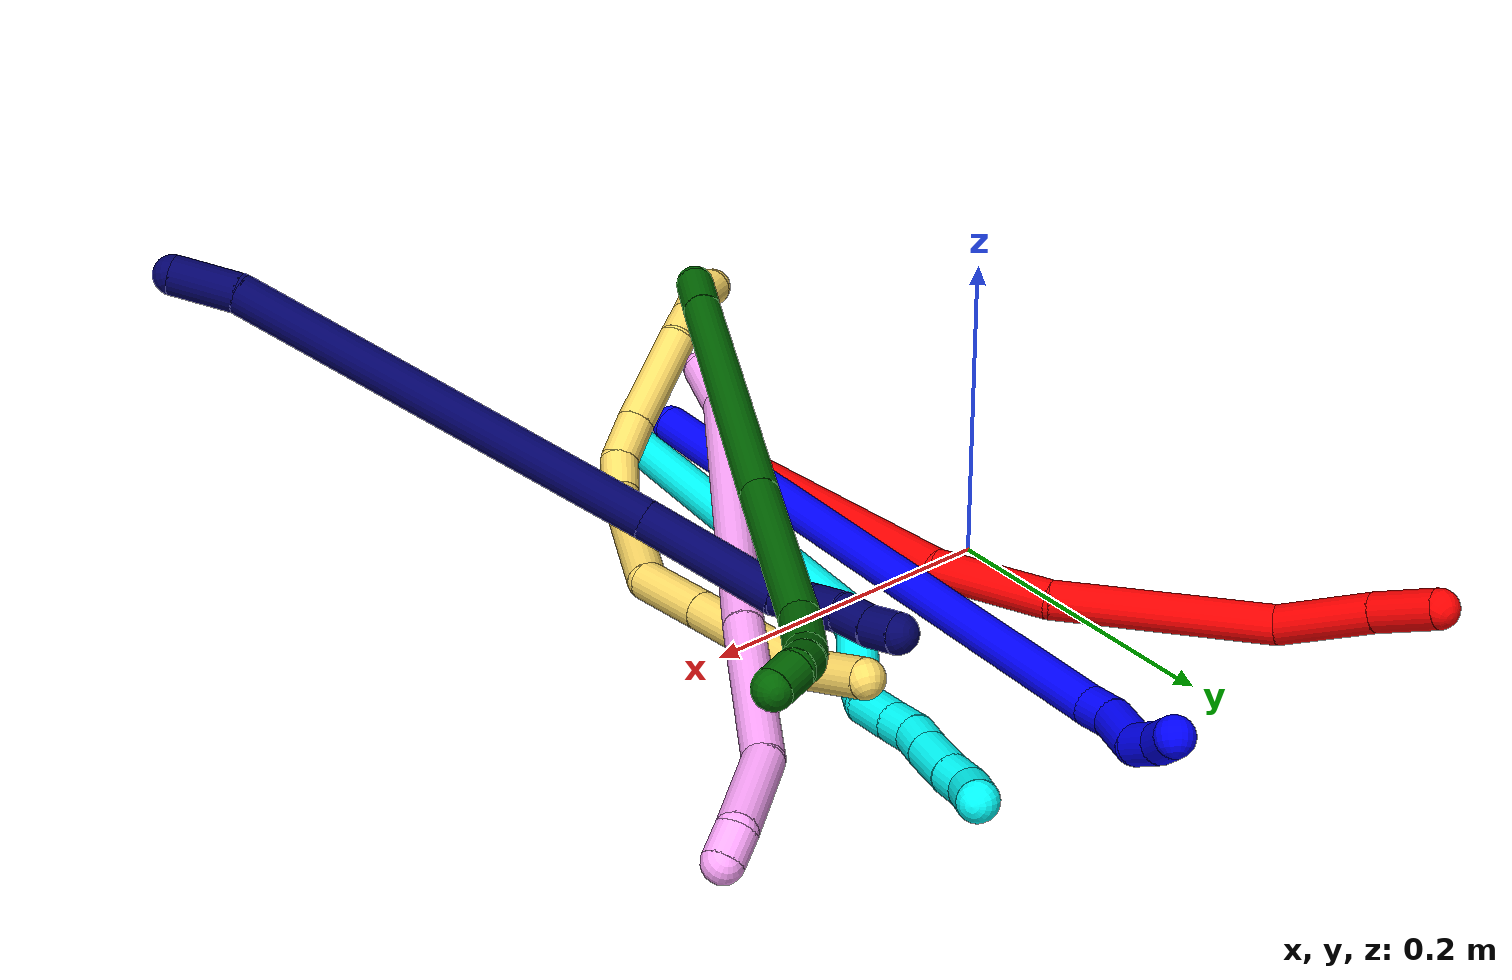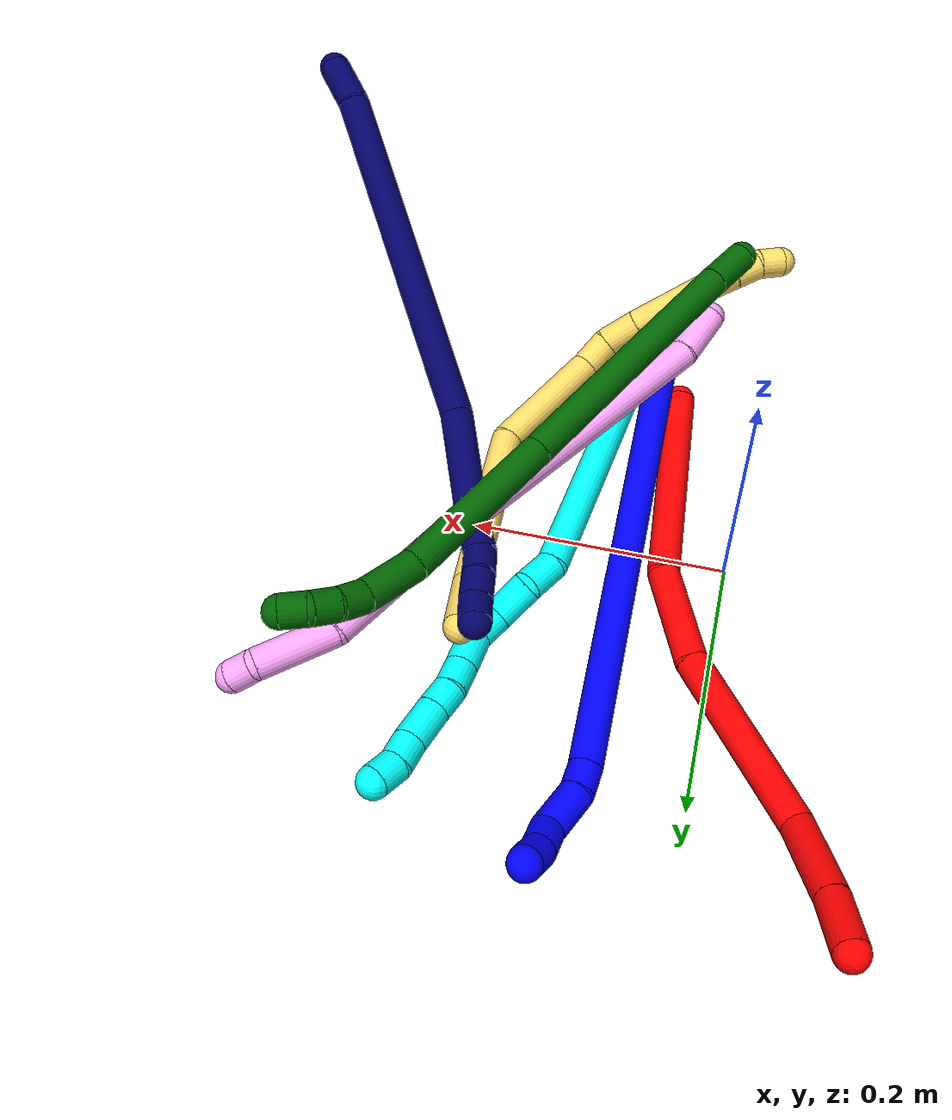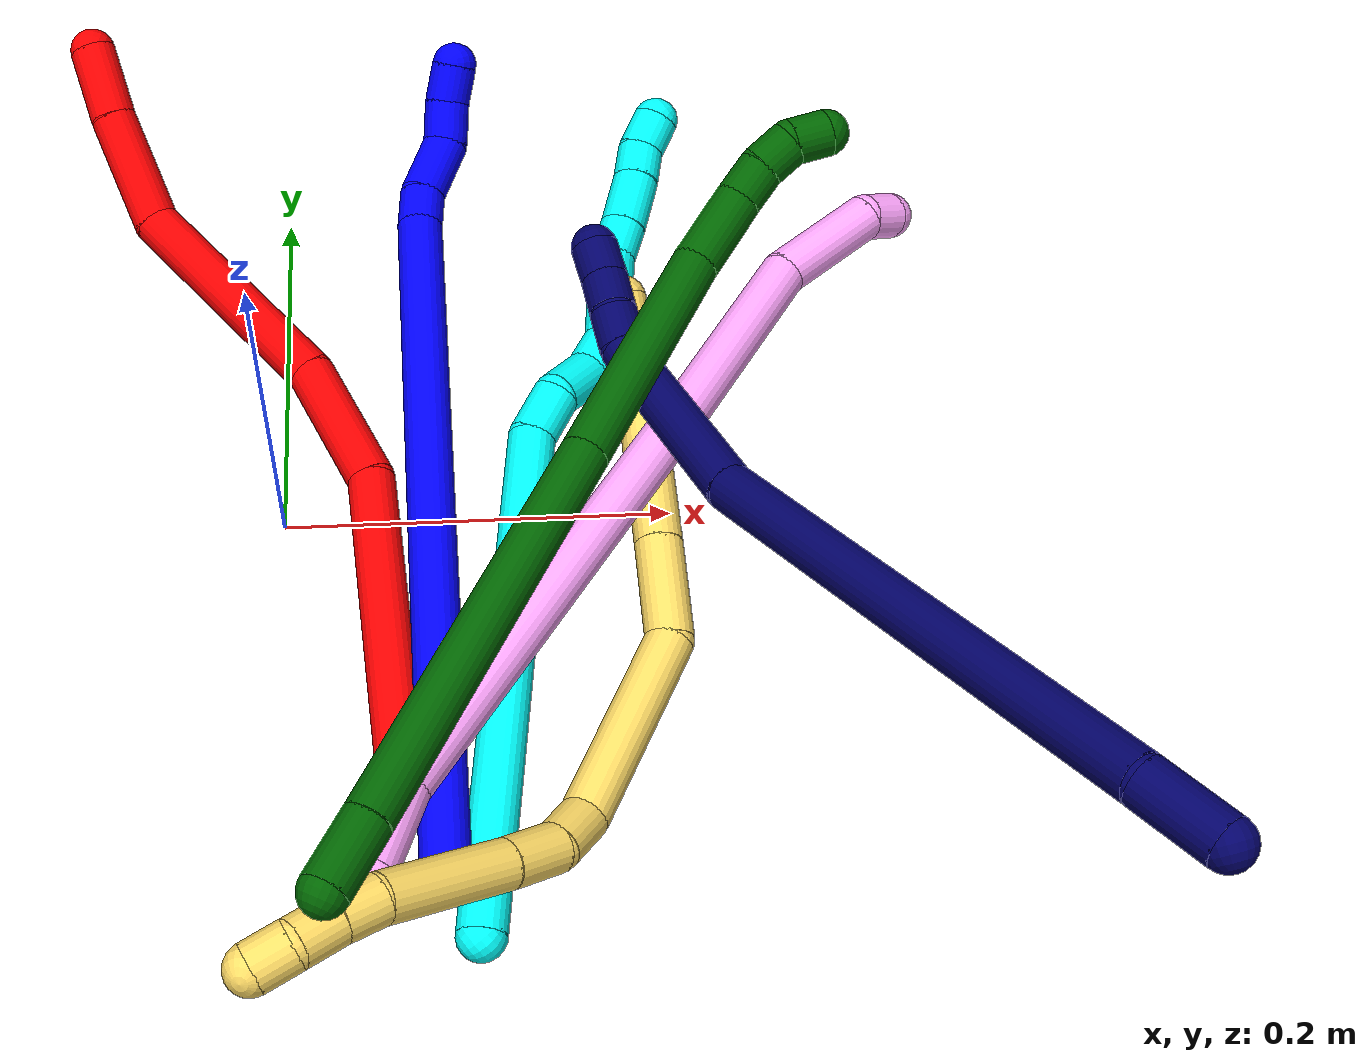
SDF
<sdf version="1.7">
 <world name="default">
  <plugin name="TubeGeneratorPlugin" filename="libtube_generator_plugin.so"/>
  <model name="photoneo_s_sensor">
   <static>1</static>
   <pose>0 0 2 1.57079 1.57079 3.14159</pose>
   <link name="link">
    <inertial><mass>0.1</mass></inertial>
    <sensor name="sensor" type="depth">
     <update_rate>30</update_rate>
     <camera>
      <horizontal_fov>1.22</horizontal_fov>
      <image><width>1920</width><height>1200</height><format>B8G8R8</format></image>
      <clip><near>0.1</near><far>4</far></clip>
      <depth_camera><output>points</output></depth_camera>
     </camera>
     <plugin name="camera_plugin" filename="libgazebo_ros_depth_camera.so">
      <baseline>0.2</baseline>
      <alwaysOn>1</alwaysOn>
      <updateRate>0.0</updateRate>
      <cameraName>camera_ir</cameraName>
      <imageTopicName>/camera/color/image_raw</imageTopicName>
      <cameraInfoTopicName>/camera/color/camera_info</cameraInfoTopicName>
      <depthImageTopicName>/camera/depth/image_raw</depthImageTopicName>
      <depthImageCameraInfoTopicName>/camera/depth/camera_info</depthImageCameraInfoTopicName>
      <pointCloudTopicName>/camera/depth/points</pointCloudTopicName>
      <frameName>fr_optical</frameName>
      <pointCloudCutoff>0.1</pointCloudCutoff>
      <pointCloudCutoffMax>2.0</pointCloudCutoffMax>
      <distortionK1>0</distortionK1>
      <distortionK2>0</distortionK2>
      <distortionK3>0</distortionK3>
      <distortionT1>0</distortionT1>
      <distortionT2>0</distortionT2>
      <CxPrime>0</CxPrime>
      <Cx>0</Cx>
      <Cy>0</Cy>
      <focalLength>0</focalLength>
      <hackBaseline>0</hackBaseline>
     </plugin>
    </sensor>
   </link>
  </model>
  <gravity>0 0 -9.8</gravity>
  <magnetic_field>6e-06 2.3e-05 -4.2e-05</magnetic_field>
  <atmosphere type="adiabatic"/>
  <physics name="default_physics" default="0" type="ode">
   <max_step_size>0.003</max_step_size>
   <real_time_factor>1</real_time_factor>
   <real_time_update_rate>1000</real_time_update_rate>
   <max_contacts>10000</max_contacts>
   <ode>
    <solver>
     <type>quick</type>
     <iters>100</iters>
     <sor>1.3</sor>
     <use_dynamic_moi_rescaling>0</use_dynamic_moi_rescaling>
    </solver>
    <constraints>
     <contact_max_correcting_vel>0</contact_max_correcting_vel>
     <contact_surface_layer>0.001</contact_surface_layer>
     <cfm>0</cfm>
     <erp>0.2</erp>
    </constraints>
   </ode>
  </physics>
  <scene><ambient>0.4 0.4 0.4 1</ambient><background>0.7 0.7 0.7 1</background><shadows>0</shadows></scene>
  <audio><device>default</device></audio>
  <spherical_coordinates>
   <surface_model>EARTH_WGS84</surface_model>
   <latitude_deg>0</latitude_deg>
   <longitude_deg>0</longitude_deg>
   <elevation>0</elevation>
   <heading_deg>0</heading_deg>
  </spherical_coordinates>
  <model name="bin">
   <static>1</static>
   <link name="bottom">
    <collision name="collision-bottom">
     <pose>0 0 -0.01 0 -0 0</pose>
     <geometry><box><size>0.8 0.6 0.02</size></box></geometry>
     <surface>
      <friction><ode><mu>100</mu><mu2>100</mu2></ode></friction>
      <contact><collide_bitmask>65535</collide_bitmask></contact>
     </surface>
    </collision>
   </link>
   <link name="west_wall">
    <collision name="collision-west_wall">
     <pose>-0.41 0 0.1 0 -0 0</pose>
     <geometry><box><size>0.02 0.6 0.2</size></box></geometry>
     <surface>
      <friction><ode><mu>100</mu><mu2>100</mu2></ode></friction>
      <contact><collide_bitmask>65535</collide_bitmask></contact>
     </surface>
    </collision>
   </link>
   <link name="east_wall">
    <collision name="collision-east_wall">
     <pose>0.41 0 0.1 0 -0 0</pose>
     <geometry><box><size>0.02 0.6 0.2</size></box></geometry>
     <surface>
      <friction><ode><mu>100</mu><mu2>100</mu2></ode></friction>
      <contact><collide_bitmask>65535</collide_bitmask></contact>
     </surface>
    </collision>
   </link>
   <link name="south_wall">
    <collision name="collision-south_wall">
     <pose>0 -0.31 0.1 0 -0 0</pose>
     <geometry><box><size>0.8 0.02 0.2</size></box></geometry>
     <surface>
      <friction><ode><mu>100</mu><mu2>100</mu2></ode></friction>
      <contact><collide_bitmask>65535</collide_bitmask></contact>
     </surface>
    </collision>
   </link>
   <link name="north_wall">
    <collision name="collision-north_wall">
     <pose>0 0.31 0.1 0 -0 0</pose>
     <geometry><box><size>0.8 0.02 0.2</size></box></geometry>
     <surface>
      <friction><ode><mu>100</mu><mu2>100</mu2></ode></friction>
      <contact><collide_bitmask>65535</collide_bitmask></contact>
     </surface>
    </collision>
   </link>
  </model>
  <model name="1">
   <static>0</static>
   <link name="1">
    <collision name="collision-cylinder-e_1_1_4">
     <pose>-0.087828 0.131945 0.120227 -0.831834 -0.457242 0.204831</pose>
     <geometry><cylinder><radius>0.0125</radius><length>0.397883</length></cylinder></geometry>
     <surface>
      <friction><ode><mu>1.16</mu><mu2>1.16</mu2><slip1>0</slip1><slip2>0</slip2></ode></friction>
      <contact><ode><kp>1e+06</kp><kd>1</kd><max_vel>0</max_vel><min_depth>0.001</min_depth></ode></contact>
     </surface>
    </collision>
    <visual name="visual-cylinder-e_1_1_4">
     <pose>-0.087828 0.131945 0.120227 -0.831834 -0.457242 0.204831</pose>
     <geometry><cylinder><radius>0.0125</radius><length>0.397883</length></cylinder></geometry>
     <material><ambient>0 0 1 1</ambient></material>
    </visual>
    <collision name="collision-cylinder-e_2_4_5">
     <pose>-0.182317 0.270169 0.245925 -0.853988 -0.674672 0.316498</pose>
     <geometry><cylinder><radius>0.0125</radius><length>0.021328</length></cylinder></geometry>
     <surface>
      <friction><ode><mu>1.16</mu><mu2>1.16</mu2><slip1>0</slip1><slip2>0</slip2></ode></friction>
      <contact><ode><kp>1e+06</kp><kd>1</kd><max_vel>0</max_vel><min_depth>0.001</min_depth></ode></contact>
     </surface>
    </collision>
    <visual name="visual-cylinder-e_2_4_5">
     <pose>-0.182317 0.270169 0.245925 -0.853988 -0.674672 0.316498</pose>
     <geometry><cylinder><radius>0.0125</radius><length>0.021328</length></cylinder></geometry>
     <material><ambient>0 0 1 1</ambient></material>
    </visual>
    <collision name="collision-cylinder-e_3_5_6">
     <pose>-0.201928 0.281911 0.261816 -0.482958 -0.833285 0.217131</pose>
     <geometry><cylinder><radius>0.0125</radius><length>0.034995</length></cylinder></geometry>
     <surface>
      <friction><ode><mu>1.16</mu><mu2>1.16</mu2><slip1>0</slip1><slip2>0</slip2></ode></friction>
      <contact><ode><kp>1e+06</kp><kd>1</kd><max_vel>0</max_vel><min_depth>0.001</min_depth></ode></contact>
     </surface>
    </collision>
    <visual name="visual-cylinder-e_3_5_6">
     <pose>-0.201928 0.281911 0.261816 -0.482958 -0.833285 0.217131</pose>
     <geometry><cylinder><radius>0.0125</radius><length>0.034995</length></cylinder></geometry>
     <material><ambient>0 0 1 1</ambient></material>
    </visual>
    <collision name="collision-cylinder-e_4_6_7">
     <pose>-0.224983 0.293827 0.274083 -1.29211 -0.984528 0.768537</pose>
     <geometry><cylinder><radius>0.0125</radius><length>0.024259</length></cylinder></geometry>
     <surface>
      <friction><ode><mu>1.16</mu><mu2>1.16</mu2><slip1>0</slip1><slip2>0</slip2></ode></friction>
      <contact><ode><kp>1e+06</kp><kd>1</kd><max_vel>0</max_vel><min_depth>0.001</min_depth></ode></contact>
     </surface>
    </collision>
    <visual name="visual-cylinder-e_4_6_7">
     <pose>-0.224983 0.293827 0.274083 -1.29211 -0.984528 0.768537</pose>
     <geometry><cylinder><radius>0.0125</radius><length>0.024259</length></cylinder></geometry>
     <material><ambient>0 0 1 1</ambient></material>
    </visual>
    <collision name="collision-cylinder-e_5_7_2">
     <pose>-0.245211 0.303927 0.276314 -1.46575 -1.22314 1.1261</pose>
     <geometry><cylinder><radius>0.0125</radius><length>0.021534</length></cylinder></geometry>
     <surface>
      <friction><ode><mu>1.16</mu><mu2>1.16</mu2><slip1>0</slip1><slip2>0</slip2></ode></friction>
      <contact><ode><kp>1e+06</kp><kd>1</kd><max_vel>0</max_vel><min_depth>0.001</min_depth></ode></contact>
     </surface>
    </collision>
    <visual name="visual-cylinder-e_5_7_2">
     <pose>-0.245211 0.303927 0.276314 -1.46575 -1.22314 1.1261</pose>
     <geometry><cylinder><radius>0.0125</radius><length>0.021534</length></cylinder></geometry>
     <material><ambient>0 0 1 1</ambient></material>
    </visual>
    <collision name="collision-sphere-2">
     <pose>-0.255334 0.307575 0.276698 0 -0 0</pose>
     <geometry><sphere><radius>0.0125</radius></sphere></geometry>
     <surface>
      <friction><ode><mu>1.16</mu><mu2>1.16</mu2><slip1>0</slip1><slip2>0</slip2></ode></friction>
      <contact><ode><kp>1e+06</kp><kd>1</kd><max_vel>0</max_vel><min_depth>0.001</min_depth></ode></contact>
     </surface>
    </collision>
    <visual name="visual-sphere-2">
     <pose>-0.255334 0.307575 0.276698 0 -0 0</pose>
     <geometry><sphere><radius>0.0125</radius></sphere></geometry>
     <material><ambient>0 0 1 1</ambient></material>
    </visual>
    <collision name="collision-sphere-7">
     <pose>-0.235088 0.300279 0.275929 0 -0 0</pose>
     <geometry><sphere><radius>0.0125</radius></sphere></geometry>
     <surface>
      <friction><ode><mu>1.16</mu><mu2>1.16</mu2><slip1>0</slip1><slip2>0</slip2></ode></friction>
      <contact><ode><kp>1e+06</kp><kd>1</kd><max_vel>0</max_vel><min_depth>0.001</min_depth></ode></contact>
     </surface>
    </collision>
    <visual name="visual-sphere-7">
     <pose>-0.235088 0.300279 0.275929 0 -0 0</pose>
     <geometry><sphere><radius>0.0125</radius></sphere></geometry>
     <material><ambient>0 0 1 1</ambient></material>
    </visual>
    <collision name="collision-sphere-6">
     <pose>-0.214879 0.287375 0.272237 0 -0 0</pose>
     <geometry><sphere><radius>0.0125</radius></sphere></geometry>
     <surface>
      <friction><ode><mu>1.16</mu><mu2>1.16</mu2><slip1>0</slip1><slip2>0</slip2></ode></friction>
      <contact><ode><kp>1e+06</kp><kd>1</kd><max_vel>0</max_vel><min_depth>0.001</min_depth></ode></contact>
     </surface>
    </collision>
    <visual name="visual-sphere-6">
     <pose>-0.214879 0.287375 0.272237 0 -0 0</pose>
     <geometry><sphere><radius>0.0125</radius></sphere></geometry>
     <material><ambient>0 0 1 1</ambient></material>
    </visual>
    <collision name="collision-sphere-5">
     <pose>-0.188978 0.276447 0.251396 0 -0 0</pose>
     <geometry><sphere><radius>0.0125</radius></sphere></geometry>
     <surface>
      <friction><ode><mu>1.16</mu><mu2>1.16</mu2><slip1>0</slip1><slip2>0</slip2></ode></friction>
      <contact><ode><kp>1e+06</kp><kd>1</kd><max_vel>0</max_vel><min_depth>0.001</min_depth></ode></contact>
     </surface>
    </collision>
    <visual name="visual-sphere-5">
     <pose>-0.188978 0.276447 0.251396 0 -0 0</pose>
     <geometry><sphere><radius>0.0125</radius></sphere></geometry>
     <material><ambient>0 0 1 1</ambient></material>
    </visual>
    <collision name="collision-sphere-1">
     <geometry><sphere><radius>0.0125</radius></sphere></geometry>
     <surface>
      <friction><ode><mu>1.16</mu><mu2>1.16</mu2><slip1>0</slip1><slip2>0</slip2></ode></friction>
      <contact><ode><kp>1e+06</kp><kd>1</kd><max_vel>0</max_vel><min_depth>0.001</min_depth></ode></contact>
     </surface>
    </collision>
    <visual name="visual-sphere-1">
     <geometry><sphere><radius>0.0125</radius></sphere></geometry>
     <material><ambient>0 0 1 1</ambient></material>
    </visual>
    <collision name="collision-sphere-4">
     <pose>-0.175655 0.26389 0.240454 0 -0 0</pose>
     <geometry><sphere><radius>0.0125</radius></sphere></geometry>
     <surface>
      <friction><ode><mu>1.16</mu><mu2>1.16</mu2><slip1>0</slip1><slip2>0</slip2></ode></friction>
      <contact><ode><kp>1e+06</kp><kd>1</kd><max_vel>0</max_vel><min_depth>0.001</min_depth></ode></contact>
     </surface>
    </collision>
    <visual name="visual-sphere-4">
     <pose>-0.175655 0.26389 0.240454 0 -0 0</pose>
     <geometry><sphere><radius>0.0125</radius></sphere></geometry>
     <material><ambient>0 0 1 1</ambient></material>
    </visual>
    <inertial>
     <pose>-0.113277 0.163599 0.149686 0 -0 0</pose>
     <mass>0.5</mass>
     <inertia>
      <ixx>0.005574</ixx>
      <ixy>0</ixy>
      <ixz>0</ixz>
      <iyy>0.004817</iyy>
      <iyz>0</iyz>
      <izz>-0.001142</izz>
     </inertia>
    </inertial>
   </link>
   <pose>0.080146 -0.209373 0.028054 3.0215 0.806559 -2.37328</pose>
  </model>
  <model name="2">
   <static>0</static>
   <link name="2">
    <collision name="collision-cylinder-e_1_1_4">
     <pose>-0.005502 0.024894 0.084853 -0.285368 -0.062134 0.008929</pose>
     <geometry><cylinder><radius>0.0125</radius><length>0.177199</length></cylinder></geometry>
     <surface>
      <friction><ode><mu>1.16</mu><mu2>1.16</mu2><slip1>0</slip1><slip2>0</slip2></ode></friction>
      <contact><ode><kp>1e+06</kp><kd>1</kd><max_vel>0</max_vel><min_depth>0.001</min_depth></ode></contact>
     </surface>
    </collision>
    <visual name="visual-cylinder-e_1_1_4">
     <pose>-0.005502 0.024894 0.084853 -0.285368 -0.062134 0.008929</pose>
     <geometry><cylinder><radius>0.0125</radius><length>0.177199</length></cylinder></geometry>
     <material><ambient>1 0 0 1</ambient></material>
    </visual>
    <collision name="collision-cylinder-e_2_4_5">
     <pose>-0.014099 0.072513 0.200652 -0.633388 -0.080448 0.026377</pose>
     <geometry><cylinder><radius>0.0125</radius><length>0.077039</length></cylinder></geometry>
     <surface>
      <friction><ode><mu>1.16</mu><mu2>1.16</mu2><slip1>0</slip1><slip2>0</slip2></ode></friction>
      <contact><ode><kp>1e+06</kp><kd>1</kd><max_vel>0</max_vel><min_depth>0.001</min_depth></ode></contact>
     </surface>
    </collision>
    <visual name="visual-cylinder-e_2_4_5">
     <pose>-0.014099 0.072513 0.200652 -0.633388 -0.080448 0.026377</pose>
     <geometry><cylinder><radius>0.0125</radius><length>0.077039</length></cylinder></geometry>
     <material><ambient>1 0 0 1</ambient></material>
    </visual>
    <collision name="collision-cylinder-e_3_5_6">
     <pose>-0.025948 0.1486 0.275103 -0.886838 -0.126476 0.060134</pose>
     <geometry><cylinder><radius>0.0125</radius><length>0.138805</length></cylinder></geometry>
     <surface>
      <friction><ode><mu>1.16</mu><mu2>1.16</mu2><slip1>0</slip1><slip2>0</slip2></ode></friction>
      <contact><ode><kp>1e+06</kp><kd>1</kd><max_vel>0</max_vel><min_depth>0.001</min_depth></ode></contact>
     </surface>
    </collision>
    <visual name="visual-cylinder-e_3_5_6">
     <pose>-0.025948 0.1486 0.275103 -0.886838 -0.126476 0.060134</pose>
     <geometry><cylinder><radius>0.0125</radius><length>0.138805</length></cylinder></geometry>
     <material><ambient>1 0 0 1</ambient></material>
    </visual>
    <collision name="collision-cylinder-e_4_6_7">
     <pose>-0.050906 0.216665 0.342757 -0.546809 -0.520365 0.149032</pose>
     <geometry><cylinder><radius>0.0125</radius><length>0.065176</length></cylinder></geometry>
     <surface>
      <friction><ode><mu>1.16</mu><mu2>1.16</mu2><slip1>0</slip1><slip2>0</slip2></ode></friction>
      <contact><ode><kp>1e+06</kp><kd>1</kd><max_vel>0</max_vel><min_depth>0.001</min_depth></ode></contact>
     </surface>
    </collision>
    <visual name="visual-cylinder-e_4_6_7">
     <pose>-0.050906 0.216665 0.342757 -0.546809 -0.520365 0.149032</pose>
     <geometry><cylinder><radius>0.0125</radius><length>0.065176</length></cylinder></geometry>
     <material><ambient>1 0 0 1</ambient></material>
    </visual>
    <collision name="collision-cylinder-e_5_7_2">
     <pose>-0.076787 0.239368 0.383604 -0.446927 -0.481739 0.111532</pose>
     <geometry><cylinder><radius>0.0125</radius><length>0.04178</length></cylinder></geometry>
     <surface>
      <friction><ode><mu>1.16</mu><mu2>1.16</mu2><slip1>0</slip1><slip2>0</slip2></ode></friction>
      <contact><ode><kp>1e+06</kp><kd>1</kd><max_vel>0</max_vel><min_depth>0.001</min_depth></ode></contact>
     </surface>
    </collision>
    <visual name="visual-cylinder-e_5_7_2">
     <pose>-0.076787 0.239368 0.383604 -0.446927 -0.481739 0.111532</pose>
     <geometry><cylinder><radius>0.0125</radius><length>0.04178</length></cylinder></geometry>
     <material><ambient>1 0 0 1</ambient></material>
    </visual>
    <collision name="collision-sphere-2">
     <pose>-0.086466 0.247369 0.400298 0 -0 0</pose>
     <geometry><sphere><radius>0.0125</radius></sphere></geometry>
     <surface>
      <friction><ode><mu>1.16</mu><mu2>1.16</mu2><slip1>0</slip1><slip2>0</slip2></ode></friction>
      <contact><ode><kp>1e+06</kp><kd>1</kd><max_vel>0</max_vel><min_depth>0.001</min_depth></ode></contact>
     </surface>
    </collision>
    <visual name="visual-sphere-2">
     <pose>-0.086466 0.247369 0.400298 0 -0 0</pose>
     <geometry><sphere><radius>0.0125</radius></sphere></geometry>
     <material><ambient>1 0 0 1</ambient></material>
    </visual>
    <collision name="collision-sphere-7">
     <pose>-0.067108 0.231367 0.366909 0 -0 0</pose>
     <geometry><sphere><radius>0.0125</radius></sphere></geometry>
     <surface>
      <friction><ode><mu>1.16</mu><mu2>1.16</mu2><slip1>0</slip1><slip2>0</slip2></ode></friction>
      <contact><ode><kp>1e+06</kp><kd>1</kd><max_vel>0</max_vel><min_depth>0.001</min_depth></ode></contact>
     </surface>
    </collision>
    <visual name="visual-sphere-7">
     <pose>-0.067108 0.231367 0.366909 0 -0 0</pose>
     <geometry><sphere><radius>0.0125</radius></sphere></geometry>
     <material><ambient>1 0 0 1</ambient></material>
    </visual>
    <collision name="collision-sphere-6">
     <pose>-0.034703 0.201963 0.318606 0 -0 0</pose>
     <geometry><sphere><radius>0.0125</radius></sphere></geometry>
     <surface>
      <friction><ode><mu>1.16</mu><mu2>1.16</mu2><slip1>0</slip1><slip2>0</slip2></ode></friction>
      <contact><ode><kp>1e+06</kp><kd>1</kd><max_vel>0</max_vel><min_depth>0.001</min_depth></ode></contact>
     </surface>
    </collision>
    <visual name="visual-sphere-6">
     <pose>-0.034703 0.201963 0.318606 0 -0 0</pose>
     <geometry><sphere><radius>0.0125</radius></sphere></geometry>
     <material><ambient>1 0 0 1</ambient></material>
    </visual>
    <collision name="collision-sphere-5">
     <pose>-0.017194 0.095238 0.2316 0 -0 0</pose>
     <geometry><sphere><radius>0.0125</radius></sphere></geometry>
     <surface>
      <friction><ode><mu>1.16</mu><mu2>1.16</mu2><slip1>0</slip1><slip2>0</slip2></ode></friction>
      <contact><ode><kp>1e+06</kp><kd>1</kd><max_vel>0</max_vel><min_depth>0.001</min_depth></ode></contact>
     </surface>
    </collision>
    <visual name="visual-sphere-5">
     <pose>-0.017194 0.095238 0.2316 0 -0 0</pose>
     <geometry><sphere><radius>0.0125</radius></sphere></geometry>
     <material><ambient>1 0 0 1</ambient></material>
    </visual>
    <collision name="collision-sphere-1">
     <geometry><sphere><radius>0.0125</radius></sphere></geometry>
     <surface>
      <friction><ode><mu>1.16</mu><mu2>1.16</mu2><slip1>0</slip1><slip2>0</slip2></ode></friction>
      <contact><ode><kp>1e+06</kp><kd>1</kd><max_vel>0</max_vel><min_depth>0.001</min_depth></ode></contact>
     </surface>
    </collision>
    <visual name="visual-sphere-1">
     <geometry><sphere><radius>0.0125</radius></sphere></geometry>
     <material><ambient>1 0 0 1</ambient></material>
    </visual>
    <collision name="collision-sphere-4">
     <pose>-0.011003 0.049787 0.169705 0 -0 0</pose>
     <geometry><sphere><radius>0.0125</radius></sphere></geometry>
     <surface>
      <friction><ode><mu>1.16</mu><mu2>1.16</mu2><slip1>0</slip1><slip2>0</slip2></ode></friction>
      <contact><ode><kp>1e+06</kp><kd>1</kd><max_vel>0</max_vel><min_depth>0.001</min_depth></ode></contact>
     </surface>
    </collision>
    <visual name="visual-sphere-4">
     <pose>-0.011003 0.049787 0.169705 0 -0 0</pose>
     <geometry><sphere><radius>0.0125</radius></sphere></geometry>
     <material><ambient>1 0 0 1</ambient></material>
    </visual>
    <inertial>
     <pose>-0.024378 0.109492 0.214092 0 -0 0</pose>
     <mass>0.5</mass>
     <inertia>
      <ixx>0.000782</ixx>
      <ixy>0</ixy>
      <ixz>0</ixz>
      <iyy>0.000702</iyy>
      <iyz>0</iyz>
      <izz>-0.000238</izz>
     </inertia>
    </inertial>
   </link>
   <pose>0.059951 -0.157051 0.011496 -1.63915 1.41975 -0.276962</pose>
  </model>
  <model name="3">
   <static>0</static>
   <link name="3">
    <collision name="collision-cylinder-e_1_1_4">
     <pose>0.004925 0.107687 0.08381 -0.909442 0.036074 -0.017638</pose>
     <geometry><cylinder><radius>0.0125</radius><length>0.273092</length></cylinder></geometry>
     <surface>
      <friction><ode><mu>1.16</mu><mu2>1.16</mu2><slip1>0</slip1><slip2>0</slip2></ode></friction>
      <contact><ode><kp>1e+06</kp><kd>1</kd><max_vel>0</max_vel><min_depth>0.001</min_depth></ode></contact>
     </surface>
    </collision>
    <visual name="visual-cylinder-e_1_1_4">
     <pose>0.004925 0.107687 0.08381 -0.909442 0.036074 -0.017638</pose>
     <geometry><cylinder><radius>0.0125</radius><length>0.273092</length></cylinder></geometry>
     <material><ambient>0.003922 1 0.996078 1</ambient></material>
    </visual>
    <collision name="collision-cylinder-e_2_4_5">
     <pose>0.01145 0.222321 0.179661 -0.523342 0.11464 -0.030733</pose>
     <geometry><cylinder><radius>0.0125</radius><length>0.027987</length></cylinder></geometry>
     <surface>
      <friction><ode><mu>1.16</mu><mu2>1.16</mu2><slip1>0</slip1><slip2>0</slip2></ode></friction>
      <contact><ode><kp>1e+06</kp><kd>1</kd><max_vel>0</max_vel><min_depth>0.001</min_depth></ode></contact>
     </surface>
    </collision>
    <visual name="visual-cylinder-e_2_4_5">
     <pose>0.01145 0.222321 0.179661 -0.523342 0.11464 -0.030733</pose>
     <geometry><cylinder><radius>0.0125</radius><length>0.027987</length></cylinder></geometry>
     <material><ambient>0.003922 1 0.996078 1</ambient></material>
    </visual>
    <collision name="collision-cylinder-e_3_5_6">
     <pose>0.022306 0.235773 0.202808 -0.529772 0.623421 -0.174365</pose>
     <geometry><cylinder><radius>0.0125</radius><length>0.031704</length></cylinder></geometry>
     <surface>
      <friction><ode><mu>1.16</mu><mu2>1.16</mu2><slip1>0</slip1><slip2>0</slip2></ode></friction>
      <contact><ode><kp>1e+06</kp><kd>1</kd><max_vel>0</max_vel><min_depth>0.001</min_depth></ode></contact>
     </surface>
    </collision>
    <visual name="visual-cylinder-e_3_5_6">
     <pose>0.022306 0.235773 0.202808 -0.529772 0.623421 -0.174365</pose>
     <geometry><cylinder><radius>0.0125</radius><length>0.031704</length></cylinder></geometry>
     <material><ambient>0.003922 1 0.996078 1</ambient></material>
    </visual>
    <collision name="collision-cylinder-e_4_6_7">
     <pose>0.033992 0.248415 0.22385 -0.553411 0.20527 -0.058484</pose>
     <geometry><cylinder><radius>0.0125</radius><length>0.02386</length></cylinder></geometry>
     <surface>
      <friction><ode><mu>1.16</mu><mu2>1.16</mu2><slip1>0</slip1><slip2>0</slip2></ode></friction>
      <contact><ode><kp>1e+06</kp><kd>1</kd><max_vel>0</max_vel><min_depth>0.001</min_depth></ode></contact>
     </surface>
    </collision>
    <visual name="visual-cylinder-e_4_6_7">
     <pose>0.033992 0.248415 0.22385 -0.553411 0.20527 -0.058484</pose>
     <geometry><cylinder><radius>0.0125</radius><length>0.02386</length></cylinder></geometry>
     <material><ambient>0.003922 1 0.996078 1</ambient></material>
    </visual>
    <collision name="collision-cylinder-e_5_7_8">
     <pose>0.035342 0.266265 0.243169 -0.895375 -0.071931 0.034553</pose>
     <geometry><cylinder><radius>0.0125</radius><length>0.030092</length></cylinder></geometry>
     <surface>
      <friction><ode><mu>1.16</mu><mu2>1.16</mu2><slip1>0</slip1><slip2>0</slip2></ode></friction>
      <contact><ode><kp>1e+06</kp><kd>1</kd><max_vel>0</max_vel><min_depth>0.001</min_depth></ode></contact>
     </surface>
    </collision>
    <visual name="visual-cylinder-e_5_7_8">
     <pose>0.035342 0.266265 0.243169 -0.895375 -0.071931 0.034553</pose>
     <geometry><cylinder><radius>0.0125</radius><length>0.030092</length></cylinder></geometry>
     <material><ambient>0.003922 1 0.996078 1</ambient></material>
    </visual>
    <collision name="collision-cylinder-e_6_8_9">
     <pose>0.033155 0.286081 0.259393 -0.869603 -0.103885 0.048283</pose>
     <geometry><cylinder><radius>0.0125</radius><length>0.021326</length></cylinder></geometry>
     <surface>
      <friction><ode><mu>1.16</mu><mu2>1.16</mu2><slip1>0</slip1><slip2>0</slip2></ode></friction>
      <contact><ode><kp>1e+06</kp><kd>1</kd><max_vel>0</max_vel><min_depth>0.001</min_depth></ode></contact>
     </surface>
    </collision>
    <visual name="visual-cylinder-e_6_8_9">
     <pose>0.033155 0.286081 0.259393 -0.869603 -0.103885 0.048283</pose>
     <geometry><cylinder><radius>0.0125</radius><length>0.021326</length></cylinder></geometry>
     <material><ambient>0.003922 1 0.996078 1</ambient></material>
    </visual>
    <collision name="collision-cylinder-e_7_9_10">
     <pose>0.03236 0.300639 0.274285 -0.675833 0.030047 -0.010559</pose>
     <geometry><cylinder><radius>0.0125</radius><length>0.020647</length></cylinder></geometry>
     <surface>
      <friction><ode><mu>1.16</mu><mu2>1.16</mu2><slip1>0</slip1><slip2>0</slip2></ode></friction>
      <contact><ode><kp>1e+06</kp><kd>1</kd><max_vel>0</max_vel><min_depth>0.001</min_depth></ode></contact>
     </surface>
    </collision>
    <visual name="visual-cylinder-e_7_9_10">
     <pose>0.03236 0.300639 0.274285 -0.675833 0.030047 -0.010559</pose>
     <geometry><cylinder><radius>0.0125</radius><length>0.020647</length></cylinder></geometry>
     <material><ambient>0.003922 1 0.996078 1</ambient></material>
    </visual>
    <collision name="collision-cylinder-e_8_10_11">
     <pose>0.032638 0.317194 0.293895 -0.718173 -0.002083 0.000782</pose>
     <geometry><cylinder><radius>0.0125</radius><length>0.030701</length></cylinder></geometry>
     <surface>
      <friction><ode><mu>1.16</mu><mu2>1.16</mu2><slip1>0</slip1><slip2>0</slip2></ode></friction>
      <contact><ode><kp>1e+06</kp><kd>1</kd><max_vel>0</max_vel><min_depth>0.001</min_depth></ode></contact>
     </surface>
    </collision>
    <visual name="visual-cylinder-e_8_10_11">
     <pose>0.032638 0.317194 0.293895 -0.718173 -0.002083 0.000782</pose>
     <geometry><cylinder><radius>0.0125</radius><length>0.030701</length></cylinder></geometry>
     <material><ambient>0.003922 1 0.996078 1</ambient></material>
    </visual>
    <collision name="collision-cylinder-e_9_11_12">
     <pose>0.032034 0.334467 0.312486 -0.795301 -0.056857 0.023887</pose>
     <geometry><cylinder><radius>0.0125</radius><length>0.020121</length></cylinder></geometry>
     <surface>
      <friction><ode><mu>1.16</mu><mu2>1.16</mu2><slip1>0</slip1><slip2>0</slip2></ode></friction>
      <contact><ode><kp>1e+06</kp><kd>1</kd><max_vel>0</max_vel><min_depth>0.001</min_depth></ode></contact>
     </surface>
    </collision>
    <visual name="visual-cylinder-e_9_11_12">
     <pose>0.032034 0.334467 0.312486 -0.795301 -0.056857 0.023887</pose>
     <geometry><cylinder><radius>0.0125</radius><length>0.020121</length></cylinder></geometry>
     <material><ambient>0.003922 1 0.996078 1</ambient></material>
    </visual>
    <collision name="collision-cylinder-e_10_12_2">
     <pose>0.030598 0.346332 0.328573 -0.478061 -0.084513 0.020607</pose>
     <geometry><cylinder><radius>0.0125</radius><length>0.020472</length></cylinder></geometry>
     <surface>
      <friction><ode><mu>1.16</mu><mu2>1.16</mu2><slip1>0</slip1><slip2>0</slip2></ode></friction>
      <contact><ode><kp>1e+06</kp><kd>1</kd><max_vel>0</max_vel><min_depth>0.001</min_depth></ode></contact>
     </surface>
    </collision>
    <visual name="visual-cylinder-e_10_12_2">
     <pose>0.030598 0.346332 0.328573 -0.478061 -0.084513 0.020607</pose>
     <geometry><cylinder><radius>0.0125</radius><length>0.020472</length></cylinder></geometry>
     <material><ambient>0.003922 1 0.996078 1</ambient></material>
    </visual>
    <collision name="collision-sphere-2">
     <pose>0.029734 0.351024 0.337629 0 -0 0</pose>
     <geometry><sphere><radius>0.0125</radius></sphere></geometry>
     <surface>
      <friction><ode><mu>1.16</mu><mu2>1.16</mu2><slip1>0</slip1><slip2>0</slip2></ode></friction>
      <contact><ode><kp>1e+06</kp><kd>1</kd><max_vel>0</max_vel><min_depth>0.001</min_depth></ode></contact>
     </surface>
    </collision>
    <visual name="visual-sphere-2">
     <pose>0.029734 0.351024 0.337629 0 -0 0</pose>
     <geometry><sphere><radius>0.0125</radius></sphere></geometry>
     <material><ambient>0.003922 1 0.996078 1</ambient></material>
    </visual>
    <collision name="collision-sphere-12">
     <pose>0.031462 0.34164 0.319517 0 -0 0</pose>
     <geometry><sphere><radius>0.0125</radius></sphere></geometry>
     <surface>
      <friction><ode><mu>1.16</mu><mu2>1.16</mu2><slip1>0</slip1><slip2>0</slip2></ode></friction>
      <contact><ode><kp>1e+06</kp><kd>1</kd><max_vel>0</max_vel><min_depth>0.001</min_depth></ode></contact>
     </surface>
    </collision>
    <visual name="visual-sphere-12">
     <pose>0.031462 0.34164 0.319517 0 -0 0</pose>
     <geometry><sphere><radius>0.0125</radius></sphere></geometry>
     <material><ambient>0.003922 1 0.996078 1</ambient></material>
    </visual>
    <collision name="collision-sphere-11">
     <pose>0.032606 0.327295 0.305454 0 -0 0</pose>
     <geometry><sphere><radius>0.0125</radius></sphere></geometry>
     <surface>
      <friction><ode><mu>1.16</mu><mu2>1.16</mu2><slip1>0</slip1><slip2>0</slip2></ode></friction>
      <contact><ode><kp>1e+06</kp><kd>1</kd><max_vel>0</max_vel><min_depth>0.001</min_depth></ode></contact>
     </surface>
    </collision>
    <visual name="visual-sphere-11">
     <pose>0.032606 0.327295 0.305454 0 -0 0</pose>
     <geometry><sphere><radius>0.0125</radius></sphere></geometry>
     <material><ambient>0.003922 1 0.996078 1</ambient></material>
    </visual>
    <collision name="collision-sphere-10">
     <pose>0.03267 0.307094 0.282336 0 -0 0</pose>
     <geometry><sphere><radius>0.0125</radius></sphere></geometry>
     <surface>
      <friction><ode><mu>1.16</mu><mu2>1.16</mu2><slip1>0</slip1><slip2>0</slip2></ode></friction>
      <contact><ode><kp>1e+06</kp><kd>1</kd><max_vel>0</max_vel><min_depth>0.001</min_depth></ode></contact>
     </surface>
    </collision>
    <visual name="visual-sphere-10">
     <pose>0.03267 0.307094 0.282336 0 -0 0</pose>
     <geometry><sphere><radius>0.0125</radius></sphere></geometry>
     <material><ambient>0.003922 1 0.996078 1</ambient></material>
    </visual>
    <collision name="collision-sphere-9">
     <pose>0.032049 0.294184 0.266235 0 -0 0</pose>
     <geometry><sphere><radius>0.0125</radius></sphere></geometry>
     <surface>
      <friction><ode><mu>1.16</mu><mu2>1.16</mu2><slip1>0</slip1><slip2>0</slip2></ode></friction>
      <contact><ode><kp>1e+06</kp><kd>1</kd><max_vel>0</max_vel><min_depth>0.001</min_depth></ode></contact>
     </surface>
    </collision>
    <visual name="visual-sphere-9">
     <pose>0.032049 0.294184 0.266235 0 -0 0</pose>
     <geometry><sphere><radius>0.0125</radius></sphere></geometry>
     <material><ambient>0.003922 1 0.996078 1</ambient></material>
    </visual>
    <collision name="collision-sphere-4">
     <pose>0.009849 0.215373 0.16762 0 -0 0</pose>
     <geometry><sphere><radius>0.0125</radius></sphere></geometry>
     <surface>
      <friction><ode><mu>1.16</mu><mu2>1.16</mu2><slip1>0</slip1><slip2>0</slip2></ode></friction>
      <contact><ode><kp>1e+06</kp><kd>1</kd><max_vel>0</max_vel><min_depth>0.001</min_depth></ode></contact>
     </surface>
    </collision>
    <visual name="visual-sphere-4">
     <pose>0.009849 0.215373 0.16762 0 -0 0</pose>
     <geometry><sphere><radius>0.0125</radius></sphere></geometry>
     <material><ambient>0.003922 1 0.996078 1</ambient></material>
    </visual>
    <collision name="collision-sphere-1">
     <geometry><sphere><radius>0.0125</radius></sphere></geometry>
     <surface>
      <friction><ode><mu>1.16</mu><mu2>1.16</mu2><slip1>0</slip1><slip2>0</slip2></ode></friction>
      <contact><ode><kp>1e+06</kp><kd>1</kd><max_vel>0</max_vel><min_depth>0.001</min_depth></ode></contact>
     </surface>
    </collision>
    <visual name="visual-sphere-1">
     <geometry><sphere><radius>0.0125</radius></sphere></geometry>
     <material><ambient>0.003922 1 0.996078 1</ambient></material>
    </visual>
    <collision name="collision-sphere-8">
     <pose>0.034261 0.277977 0.252551 0 -0 0</pose>
     <geometry><sphere><radius>0.0125</radius></sphere></geometry>
     <surface>
      <friction><ode><mu>1.16</mu><mu2>1.16</mu2><slip1>0</slip1><slip2>0</slip2></ode></friction>
      <contact><ode><kp>1e+06</kp><kd>1</kd><max_vel>0</max_vel><min_depth>0.001</min_depth></ode></contact>
     </surface>
    </collision>
    <visual name="visual-sphere-8">
     <pose>0.034261 0.277977 0.252551 0 -0 0</pose>
     <geometry><sphere><radius>0.0125</radius></sphere></geometry>
     <material><ambient>0.003922 1 0.996078 1</ambient></material>
    </visual>
    <collision name="collision-sphere-5">
     <pose>0.013051 0.229269 0.191702 0 -0 0</pose>
     <geometry><sphere><radius>0.0125</radius></sphere></geometry>
     <surface>
      <friction><ode><mu>1.16</mu><mu2>1.16</mu2><slip1>0</slip1><slip2>0</slip2></ode></friction>
      <contact><ode><kp>1e+06</kp><kd>1</kd><max_vel>0</max_vel><min_depth>0.001</min_depth></ode></contact>
     </surface>
    </collision>
    <visual name="visual-sphere-5">
     <pose>0.013051 0.229269 0.191702 0 -0 0</pose>
     <geometry><sphere><radius>0.0125</radius></sphere></geometry>
     <material><ambient>0.003922 1 0.996078 1</ambient></material>
    </visual>
    <collision name="collision-sphere-6">
     <pose>0.03156 0.242276 0.213914 0 -0 0</pose>
     <geometry><sphere><radius>0.0125</radius></sphere></geometry>
     <surface>
      <friction><ode><mu>1.16</mu><mu2>1.16</mu2><slip1>0</slip1><slip2>0</slip2></ode></friction>
      <contact><ode><kp>1e+06</kp><kd>1</kd><max_vel>0</max_vel><min_depth>0.001</min_depth></ode></contact>
     </surface>
    </collision>
    <visual name="visual-sphere-6">
     <pose>0.03156 0.242276 0.213914 0 -0 0</pose>
     <geometry><sphere><radius>0.0125</radius></sphere></geometry>
     <material><ambient>0.003922 1 0.996078 1</ambient></material>
    </visual>
    <collision name="collision-sphere-7">
     <pose>0.036424 0.254553 0.233786 0 -0 0</pose>
     <geometry><sphere><radius>0.0125</radius></sphere></geometry>
     <surface>
      <friction><ode><mu>1.16</mu><mu2>1.16</mu2><slip1>0</slip1><slip2>0</slip2></ode></friction>
      <contact><ode><kp>1e+06</kp><kd>1</kd><max_vel>0</max_vel><min_depth>0.001</min_depth></ode></contact>
     </surface>
    </collision>
    <visual name="visual-sphere-7">
     <pose>0.036424 0.254553 0.233786 0 -0 0</pose>
     <geometry><sphere><radius>0.0125</radius></sphere></geometry>
     <material><ambient>0.003922 1 0.996078 1</ambient></material>
    </visual>
    <inertial>
     <pose>0.01579 0.185822 0.160471 0 -0 0</pose>
     <mass>0.5</mass>
     <inertia>
      <ixx>0.001699</ixx>
      <ixy>0</ixy>
      <ixz>0</ixz>
      <iyy>0.001064</iyy>
      <iyz>0</iyz>
      <izz>-0.001398</izz>
     </inertia>
    </inertial>
   </link>
   <pose>0.095574 -0.234003 0.011495 -0.462045 1.20747 0.073544</pose>
  </model>
  <model name="4">
   <static>0</static>
   <link name="4">
    <collision name="collision-cylinder-e_1_1_4">
     <pose>0.003941 0.020212 0.010091 -1.10777 0.172709 -0.106978</pose>
     <geometry><cylinder><radius>0.0125</radius><length>0.045865</length></cylinder></geometry>
     <surface>
      <friction><ode><mu>1.16</mu><mu2>1.16</mu2><slip1>0</slip1><slip2>0</slip2></ode></friction>
      <contact><ode><kp>1e+06</kp><kd>1</kd><max_vel>0</max_vel><min_depth>0.001</min_depth></ode></contact>
     </surface>
    </collision>
    <visual name="visual-cylinder-e_1_1_4">
     <pose>0.003941 0.020212 0.010091 -1.10777 0.172709 -0.106978</pose>
     <geometry><cylinder><radius>0.0125</radius><length>0.045865</length></cylinder></geometry>
     <material><ambient>1 0.65098 0.996078 1</ambient></material>
    </visual>
    <collision name="collision-cylinder-e_2_4_5">
     <pose>0.059525 0.141763 0.075789 -1.06892 0.420166 -0.251103</pose>
     <geometry><cylinder><radius>0.0125</radius><length>0.253209</length></cylinder></geometry>
     <surface>
      <friction><ode><mu>1.16</mu><mu2>1.16</mu2><slip1>0</slip1><slip2>0</slip2></ode></friction>
      <contact><ode><kp>1e+06</kp><kd>1</kd><max_vel>0</max_vel><min_depth>0.001</min_depth></ode></contact>
     </surface>
    </collision>
    <visual name="visual-cylinder-e_2_4_5">
     <pose>0.059525 0.141763 0.075789 -1.06892 0.420166 -0.251103</pose>
     <geometry><cylinder><radius>0.0125</radius><length>0.253209</length></cylinder></geometry>
     <material><ambient>1 0.65098 0.996078 1</ambient></material>
    </visual>
    <collision name="collision-cylinder-e_3_5_6">
     <pose>0.133103 0.292859 0.154695 -1.13291 0.379838 -0.243308</pose>
     <geometry><cylinder><radius>0.0125</radius><length>0.118317</length></cylinder></geometry>
     <surface>
      <friction><ode><mu>1.16</mu><mu2>1.16</mu2><slip1>0</slip1><slip2>0</slip2></ode></friction>
      <contact><ode><kp>1e+06</kp><kd>1</kd><max_vel>0</max_vel><min_depth>0.001</min_depth></ode></contact>
     </surface>
    </collision>
    <visual name="visual-cylinder-e_3_5_6">
     <pose>0.133103 0.292859 0.154695 -1.13291 0.379838 -0.243308</pose>
     <geometry><cylinder><radius>0.0125</radius><length>0.118317</length></cylinder></geometry>
     <material><ambient>1 0.65098 0.996078 1</ambient></material>
    </visual>
    <collision name="collision-cylinder-e_4_6_7">
     <pose>0.175527 0.363528 0.189066 -1.08373 0.713649 -0.441493</pose>
     <geometry><cylinder><radius>0.0125</radius><length>0.062602</length></cylinder></geometry>
     <surface>
      <friction><ode><mu>1.16</mu><mu2>1.16</mu2><slip1>0</slip1><slip2>0</slip2></ode></friction>
      <contact><ode><kp>1e+06</kp><kd>1</kd><max_vel>0</max_vel><min_depth>0.001</min_depth></ode></contact>
     </surface>
    </collision>
    <visual name="visual-cylinder-e_4_6_7">
     <pose>0.175527 0.363528 0.189066 -1.08373 0.713649 -0.441493</pose>
     <geometry><cylinder><radius>0.0125</radius><length>0.062602</length></cylinder></geometry>
     <material><ambient>1 0.65098 0.996078 1</ambient></material>
    </visual>
    <collision name="collision-cylinder-e_5_7_2">
     <pose>0.202981 0.391503 0.198852 -1.75131 0.770175 -0.904756</pose>
     <geometry><cylinder><radius>0.0125</radius><length>0.020007</length></cylinder></geometry>
     <surface>
      <friction><ode><mu>1.16</mu><mu2>1.16</mu2><slip1>0</slip1><slip2>0</slip2></ode></friction>
      <contact><ode><kp>1e+06</kp><kd>1</kd><max_vel>0</max_vel><min_depth>0.001</min_depth></ode></contact>
     </surface>
    </collision>
    <visual name="visual-cylinder-e_5_7_2">
     <pose>0.202981 0.391503 0.198852 -1.75131 0.770175 -0.904756</pose>
     <geometry><cylinder><radius>0.0125</radius><length>0.020007</length></cylinder></geometry>
     <material><ambient>1 0.65098 0.996078 1</ambient></material>
    </visual>
    <collision name="collision-sphere-2">
     <pose>0.209947 0.398567 0.197563 0 -0 0</pose>
     <geometry><sphere><radius>0.0125</radius></sphere></geometry>
     <surface>
      <friction><ode><mu>1.16</mu><mu2>1.16</mu2><slip1>0</slip1><slip2>0</slip2></ode></friction>
      <contact><ode><kp>1e+06</kp><kd>1</kd><max_vel>0</max_vel><min_depth>0.001</min_depth></ode></contact>
     </surface>
    </collision>
    <visual name="visual-sphere-2">
     <pose>0.209947 0.398567 0.197563 0 -0 0</pose>
     <geometry><sphere><radius>0.0125</radius></sphere></geometry>
     <material><ambient>1 0.65098 0.996078 1</ambient></material>
    </visual>
    <collision name="collision-sphere-7">
     <pose>0.196016 0.384439 0.200141 0 -0 0</pose>
     <geometry><sphere><radius>0.0125</radius></sphere></geometry>
     <surface>
      <friction><ode><mu>1.16</mu><mu2>1.16</mu2><slip1>0</slip1><slip2>0</slip2></ode></friction>
      <contact><ode><kp>1e+06</kp><kd>1</kd><max_vel>0</max_vel><min_depth>0.001</min_depth></ode></contact>
     </surface>
    </collision>
    <visual name="visual-sphere-7">
     <pose>0.196016 0.384439 0.200141 0 -0 0</pose>
     <geometry><sphere><radius>0.0125</radius></sphere></geometry>
     <material><ambient>1 0.65098 0.996078 1</ambient></material>
    </visual>
    <collision name="collision-sphere-6">
     <pose>0.155037 0.342617 0.177991 0 -0 0</pose>
     <geometry><sphere><radius>0.0125</radius></sphere></geometry>
     <surface>
      <friction><ode><mu>1.16</mu><mu2>1.16</mu2><slip1>0</slip1><slip2>0</slip2></ode></friction>
      <contact><ode><kp>1e+06</kp><kd>1</kd><max_vel>0</max_vel><min_depth>0.001</min_depth></ode></contact>
     </surface>
    </collision>
    <visual name="visual-sphere-6">
     <pose>0.155037 0.342617 0.177991 0 -0 0</pose>
     <geometry><sphere><radius>0.0125</radius></sphere></geometry>
     <material><ambient>1 0.65098 0.996078 1</ambient></material>
    </visual>
    <collision name="collision-sphere-5">
     <pose>0.111169 0.243101 0.131398 0 -0 0</pose>
     <geometry><sphere><radius>0.0125</radius></sphere></geometry>
     <surface>
      <friction><ode><mu>1.16</mu><mu2>1.16</mu2><slip1>0</slip1><slip2>0</slip2></ode></friction>
      <contact><ode><kp>1e+06</kp><kd>1</kd><max_vel>0</max_vel><min_depth>0.001</min_depth></ode></contact>
     </surface>
    </collision>
    <visual name="visual-sphere-5">
     <pose>0.111169 0.243101 0.131398 0 -0 0</pose>
     <geometry><sphere><radius>0.0125</radius></sphere></geometry>
     <material><ambient>1 0.65098 0.996078 1</ambient></material>
    </visual>
    <collision name="collision-sphere-1">
     <geometry><sphere><radius>0.0125</radius></sphere></geometry>
     <surface>
      <friction><ode><mu>1.16</mu><mu2>1.16</mu2><slip1>0</slip1><slip2>0</slip2></ode></friction>
      <contact><ode><kp>1e+06</kp><kd>1</kd><max_vel>0</max_vel><min_depth>0.001</min_depth></ode></contact>
     </surface>
    </collision>
    <visual name="visual-sphere-1">
     <geometry><sphere><radius>0.0125</radius></sphere></geometry>
     <material><ambient>1 0.65098 0.996078 1</ambient></material>
    </visual>
    <collision name="collision-sphere-4">
     <pose>0.007882 0.040425 0.020181 0 -0 0</pose>
     <geometry><sphere><radius>0.0125</radius></sphere></geometry>
     <surface>
      <friction><ode><mu>1.16</mu><mu2>1.16</mu2><slip1>0</slip1><slip2>0</slip2></ode></friction>
      <contact><ode><kp>1e+06</kp><kd>1</kd><max_vel>0</max_vel><min_depth>0.001</min_depth></ode></contact>
     </surface>
    </collision>
    <visual name="visual-sphere-4">
     <pose>0.007882 0.040425 0.020181 0 -0 0</pose>
     <geometry><sphere><radius>0.0125</radius></sphere></geometry>
     <material><ambient>1 0.65098 0.996078 1</ambient></material>
    </visual>
    <inertial>
     <pose>0.092102 0.204127 0.107542 0 -0 0</pose>
     <mass>0.5</mass>
     <inertia>
      <ixx>0.001026</ixx>
      <ixy>0</ixy>
      <ixz>0</ixz>
      <iyy>0.000528</iyy>
      <iyz>0</iyz>
      <izz>-0.001847</izz>
     </inertia>
    </inertial>
   </link>
   <pose>0.047209 -0.218161 0.05509 -0.550023 -0.015047 -0.183222</pose>
  </model>
  <model name="5">
   <static>0</static>
   <link name="5">
    <collision name="collision-cylinder-e_1_1_4">
     <pose>0.006027 -0.019495 0.013134 0.977959 0.250974 0.134042</pose>
     <geometry><cylinder><radius>0.0125</radius><length>0.048534</length></cylinder></geometry>
     <surface>
      <friction><ode><mu>1.16</mu><mu2>1.16</mu2><slip1>0</slip1><slip2>0</slip2></ode></friction>
      <contact><ode><kp>1e+06</kp><kd>1</kd><max_vel>0</max_vel><min_depth>0.001</min_depth></ode></contact>
     </surface>
    </collision>
    <visual name="visual-cylinder-e_1_1_4">
     <pose>0.006027 -0.019495 0.013134 0.977959 0.250974 0.134042</pose>
     <geometry><cylinder><radius>0.0125</radius><length>0.048534</length></cylinder></geometry>
     <material><ambient>1 0.858824 0.4 1</ambient></material>
    </visual>
    <collision name="collision-cylinder-e_2_4_5">
     <pose>0.023678 -0.069206 0.061779 0.704983 0.244327 0.090265</pose>
     <geometry><cylinder><radius>0.0125</radius><length>0.096108</length></cylinder></geometry>
     <surface>
      <friction><ode><mu>1.16</mu><mu2>1.16</mu2><slip1>0</slip1><slip2>0</slip2></ode></friction>
      <contact><ode><kp>1e+06</kp><kd>1</kd><max_vel>0</max_vel><min_depth>0.001</min_depth></ode></contact>
     </surface>
    </collision>
    <visual name="visual-cylinder-e_2_4_5">
     <pose>0.023678 -0.069206 0.061779 0.704983 0.244327 0.090265</pose>
     <geometry><cylinder><radius>0.0125</radius><length>0.096108</length></cylinder></geometry>
     <material><ambient>1 0.858824 0.4 1</ambient></material>
    </visual>
    <collision name="collision-cylinder-e_3_5_6">
     <pose>0.041571 -0.116775 0.117291 0.714672 0.232458 0.087129</pose>
     <geometry><cylinder><radius>0.0125</radius><length>0.054423</length></cylinder></geometry>
     <surface>
      <friction><ode><mu>1.16</mu><mu2>1.16</mu2><slip1>0</slip1><slip2>0</slip2></ode></friction>
      <contact><ode><kp>1e+06</kp><kd>1</kd><max_vel>0</max_vel><min_depth>0.001</min_depth></ode></contact>
     </surface>
    </collision>
    <visual name="visual-cylinder-e_3_5_6">
     <pose>0.041571 -0.116775 0.117291 0.714672 0.232458 0.087129</pose>
     <geometry><cylinder><radius>0.0125</radius><length>0.054423</length></cylinder></geometry>
     <material><ambient>1 0.858824 0.4 1</ambient></material>
    </visual>
    <collision name="collision-cylinder-e_4_6_7">
     <pose>0.035043 -0.160088 0.181523 0.530734 -0.244518 -0.066762</pose>
     <geometry><cylinder><radius>0.0125</radius><length>0.105718</length></cylinder></geometry>
     <surface>
      <friction><ode><mu>1.16</mu><mu2>1.16</mu2><slip1>0</slip1><slip2>0</slip2></ode></friction>
      <contact><ode><kp>1e+06</kp><kd>1</kd><max_vel>0</max_vel><min_depth>0.001</min_depth></ode></contact>
     </surface>
    </collision>
    <visual name="visual-cylinder-e_4_6_7">
     <pose>0.035043 -0.160088 0.181523 0.530734 -0.244518 -0.066762</pose>
     <geometry><cylinder><radius>0.0125</radius><length>0.105718</length></cylinder></geometry>
     <material><ambient>1 0.858824 0.4 1</ambient></material>
    </visual>
    <collision name="collision-cylinder-e_5_7_8">
     <pose>0.01889 -0.186587 0.239192 0.040114 -0.244567 -0.004931</pose>
     <geometry><cylinder><radius>0.0125</radius><length>0.027723</length></cylinder></geometry>
     <surface>
      <friction><ode><mu>1.16</mu><mu2>1.16</mu2><slip1>0</slip1><slip2>0</slip2></ode></friction>
      <contact><ode><kp>1e+06</kp><kd>1</kd><max_vel>0</max_vel><min_depth>0.001</min_depth></ode></contact>
     </surface>
    </collision>
    <visual name="visual-cylinder-e_5_7_8">
     <pose>0.01889 -0.186587 0.239192 0.040114 -0.244567 -0.004931</pose>
     <geometry><cylinder><radius>0.0125</radius><length>0.027723</length></cylinder></geometry>
     <material><ambient>1 0.858824 0.4 1</ambient></material>
    </visual>
    <collision name="collision-cylinder-e_6_8_9">
     <pose>0.007302 -0.184786 0.265297 -0.182692 -0.568652 0.053527</pose>
     <geometry><cylinder><radius>0.0125</radius><length>0.030574</length></cylinder></geometry>
     <surface>
      <friction><ode><mu>1.16</mu><mu2>1.16</mu2><slip1>0</slip1><slip2>0</slip2></ode></friction>
      <contact><ode><kp>1e+06</kp><kd>1</kd><max_vel>0</max_vel><min_depth>0.001</min_depth></ode></contact>
     </surface>
    </collision>
    <visual name="visual-cylinder-e_6_8_9">
     <pose>0.007302 -0.184786 0.265297 -0.182692 -0.568652 0.053527</pose>
     <geometry><cylinder><radius>0.0125</radius><length>0.030574</length></cylinder></geometry>
     <material><ambient>1 0.858824 0.4 1</ambient></material>
    </visual>
    <collision name="collision-cylinder-e_7_9_10">
     <pose>-0.021505 -0.176107 0.306154 -0.2212 -0.618769 0.070966</pose>
     <geometry><cylinder><radius>0.0125</radius><length>0.070942</length></cylinder></geometry>
     <surface>
      <friction><ode><mu>1.16</mu><mu2>1.16</mu2><slip1>0</slip1><slip2>0</slip2></ode></friction>
      <contact><ode><kp>1e+06</kp><kd>1</kd><max_vel>0</max_vel><min_depth>0.001</min_depth></ode></contact>
     </surface>
    </collision>
    <visual name="visual-cylinder-e_7_9_10">
     <pose>-0.021505 -0.176107 0.306154 -0.2212 -0.618769 0.070966</pose>
     <geometry><cylinder><radius>0.0125</radius><length>0.070942</length></cylinder></geometry>
     <material><ambient>1 0.858824 0.4 1</ambient></material>
    </visual>
    <collision name="collision-cylinder-e_8_10_11">
     <pose>-0.049088 -0.170028 0.343169 0.029501 -0.671042 -0.010288</pose>
     <geometry><cylinder><radius>0.0125</radius><length>0.022545</length></cylinder></geometry>
     <surface>
      <friction><ode><mu>1.16</mu><mu2>1.16</mu2><slip1>0</slip1><slip2>0</slip2></ode></friction>
      <contact><ode><kp>1e+06</kp><kd>1</kd><max_vel>0</max_vel><min_depth>0.001</min_depth></ode></contact>
     </surface>
    </collision>
    <visual name="visual-cylinder-e_8_10_11">
     <pose>-0.049088 -0.170028 0.343169 0.029501 -0.671042 -0.010288</pose>
     <geometry><cylinder><radius>0.0125</radius><length>0.022545</length></cylinder></geometry>
     <material><ambient>1 0.858824 0.4 1</ambient></material>
    </visual>
    <collision name="collision-cylinder-e_9_11_12">
     <pose>-0.063027 -0.171623 0.360953 0.147871 -0.653044 -0.050156</pose>
     <geometry><cylinder><radius>0.0125</radius><length>0.02281</length></cylinder></geometry>
     <surface>
      <friction><ode><mu>1.16</mu><mu2>1.16</mu2><slip1>0</slip1><slip2>0</slip2></ode></friction>
      <contact><ode><kp>1e+06</kp><kd>1</kd><max_vel>0</max_vel><min_depth>0.001</min_depth></ode></contact>
     </surface>
    </collision>
    <visual name="visual-cylinder-e_9_11_12">
     <pose>-0.063027 -0.171623 0.360953 0.147871 -0.653044 -0.050156</pose>
     <geometry><cylinder><radius>0.0125</radius><length>0.02281</length></cylinder></geometry>
     <material><ambient>1 0.858824 0.4 1</ambient></material>
    </visual>
    <collision name="collision-cylinder-e_10_12_2">
     <pose>-0.077884 -0.176117 0.375701 0.499714 -0.876874 -0.23817</pose>
     <geometry><cylinder><radius>0.0125</radius><length>0.020624</length></cylinder></geometry>
     <surface>
      <friction><ode><mu>1.16</mu><mu2>1.16</mu2><slip1>0</slip1><slip2>0</slip2></ode></friction>
      <contact><ode><kp>1e+06</kp><kd>1</kd><max_vel>0</max_vel><min_depth>0.001</min_depth></ode></contact>
     </surface>
    </collision>
    <visual name="visual-cylinder-e_10_12_2">
     <pose>-0.077884 -0.176117 0.375701 0.499714 -0.876874 -0.23817</pose>
     <geometry><cylinder><radius>0.0125</radius><length>0.020624</length></cylinder></geometry>
     <material><ambient>1 0.858824 0.4 1</ambient></material>
    </visual>
    <collision name="collision-sphere-2">
     <pose>-0.085812 -0.179278 0.38149 0 -0 0</pose>
     <geometry><sphere><radius>0.0125</radius></sphere></geometry>
     <surface>
      <friction><ode><mu>1.16</mu><mu2>1.16</mu2><slip1>0</slip1><slip2>0</slip2></ode></friction>
      <contact><ode><kp>1e+06</kp><kd>1</kd><max_vel>0</max_vel><min_depth>0.001</min_depth></ode></contact>
     </surface>
    </collision>
    <visual name="visual-sphere-2">
     <pose>-0.085812 -0.179278 0.38149 0 -0 0</pose>
     <geometry><sphere><radius>0.0125</radius></sphere></geometry>
     <material><ambient>1 0.858824 0.4 1</ambient></material>
    </visual>
    <collision name="collision-sphere-12">
     <pose>-0.069957 -0.172957 0.369912 0 -0 0</pose>
     <geometry><sphere><radius>0.0125</radius></sphere></geometry>
     <surface>
      <friction><ode><mu>1.16</mu><mu2>1.16</mu2><slip1>0</slip1><slip2>0</slip2></ode></friction>
      <contact><ode><kp>1e+06</kp><kd>1</kd><max_vel>0</max_vel><min_depth>0.001</min_depth></ode></contact>
     </surface>
    </collision>
    <visual name="visual-sphere-12">
     <pose>-0.069957 -0.172957 0.369912 0 -0 0</pose>
     <geometry><sphere><radius>0.0125</radius></sphere></geometry>
     <material><ambient>1 0.858824 0.4 1</ambient></material>
    </visual>
    <collision name="collision-sphere-11">
     <pose>-0.056097 -0.170288 0.351993 0 -0 0</pose>
     <geometry><sphere><radius>0.0125</radius></sphere></geometry>
     <surface>
      <friction><ode><mu>1.16</mu><mu2>1.16</mu2><slip1>0</slip1><slip2>0</slip2></ode></friction>
      <contact><ode><kp>1e+06</kp><kd>1</kd><max_vel>0</max_vel><min_depth>0.001</min_depth></ode></contact>
     </surface>
    </collision>
    <visual name="visual-sphere-11">
     <pose>-0.056097 -0.170288 0.351993 0 -0 0</pose>
     <geometry><sphere><radius>0.0125</radius></sphere></geometry>
     <material><ambient>1 0.858824 0.4 1</ambient></material>
    </visual>
    <collision name="collision-sphere-10">
     <pose>-0.042079 -0.169767 0.334345 0 -0 0</pose>
     <geometry><sphere><radius>0.0125</radius></sphere></geometry>
     <surface>
      <friction><ode><mu>1.16</mu><mu2>1.16</mu2><slip1>0</slip1><slip2>0</slip2></ode></friction>
      <contact><ode><kp>1e+06</kp><kd>1</kd><max_vel>0</max_vel><min_depth>0.001</min_depth></ode></contact>
     </surface>
    </collision>
    <visual name="visual-sphere-10">
     <pose>-0.042079 -0.169767 0.334345 0 -0 0</pose>
     <geometry><sphere><radius>0.0125</radius></sphere></geometry>
     <material><ambient>1 0.858824 0.4 1</ambient></material>
    </visual>
    <collision name="collision-sphere-9">
     <pose>-0.00093 -0.182446 0.277964 0 -0 0</pose>
     <geometry><sphere><radius>0.0125</radius></sphere></geometry>
     <surface>
      <friction><ode><mu>1.16</mu><mu2>1.16</mu2><slip1>0</slip1><slip2>0</slip2></ode></friction>
      <contact><ode><kp>1e+06</kp><kd>1</kd><max_vel>0</max_vel><min_depth>0.001</min_depth></ode></contact>
     </surface>
    </collision>
    <visual name="visual-sphere-9">
     <pose>-0.00093 -0.182446 0.277964 0 -0 0</pose>
     <geometry><sphere><radius>0.0125</radius></sphere></geometry>
     <material><ambient>1 0.858824 0.4 1</ambient></material>
    </visual>
    <collision name="collision-sphere-4">
     <pose>0.012053 -0.038991 0.026267 0 -0 0</pose>
     <geometry><sphere><radius>0.0125</radius></sphere></geometry>
     <surface>
      <friction><ode><mu>1.16</mu><mu2>1.16</mu2><slip1>0</slip1><slip2>0</slip2></ode></friction>
      <contact><ode><kp>1e+06</kp><kd>1</kd><max_vel>0</max_vel><min_depth>0.001</min_depth></ode></contact>
     </surface>
    </collision>
    <visual name="visual-sphere-4">
     <pose>0.012053 -0.038991 0.026267 0 -0 0</pose>
     <geometry><sphere><radius>0.0125</radius></sphere></geometry>
     <material><ambient>1 0.858824 0.4 1</ambient></material>
    </visual>
    <collision name="collision-sphere-1">
     <geometry><sphere><radius>0.0125</radius></sphere></geometry>
     <surface>
      <friction><ode><mu>1.16</mu><mu2>1.16</mu2><slip1>0</slip1><slip2>0</slip2></ode></friction>
      <contact><ode><kp>1e+06</kp><kd>1</kd><max_vel>0</max_vel><min_depth>0.001</min_depth></ode></contact>
     </surface>
    </collision>
    <visual name="visual-sphere-1">
     <geometry><sphere><radius>0.0125</radius></sphere></geometry>
     <material><ambient>1 0.858824 0.4 1</ambient></material>
    </visual>
    <collision name="collision-sphere-8">
     <pose>0.015534 -0.187126 0.252631 0 -0 0</pose>
     <geometry><sphere><radius>0.0125</radius></sphere></geometry>
     <surface>
      <friction><ode><mu>1.16</mu><mu2>1.16</mu2><slip1>0</slip1><slip2>0</slip2></ode></friction>
      <contact><ode><kp>1e+06</kp><kd>1</kd><max_vel>0</max_vel><min_depth>0.001</min_depth></ode></contact>
     </surface>
    </collision>
    <visual name="visual-sphere-8">
     <pose>0.015534 -0.187126 0.252631 0 -0 0</pose>
     <geometry><sphere><radius>0.0125</radius></sphere></geometry>
     <material><ambient>1 0.858824 0.4 1</ambient></material>
    </visual>
    <collision name="collision-sphere-5">
     <pose>0.035302 -0.099421 0.097291 0 -0 0</pose>
     <geometry><sphere><radius>0.0125</radius></sphere></geometry>
     <surface>
      <friction><ode><mu>1.16</mu><mu2>1.16</mu2><slip1>0</slip1><slip2>0</slip2></ode></friction>
      <contact><ode><kp>1e+06</kp><kd>1</kd><max_vel>0</max_vel><min_depth>0.001</min_depth></ode></contact>
     </surface>
    </collision>
    <visual name="visual-sphere-5">
     <pose>0.035302 -0.099421 0.097291 0 -0 0</pose>
     <geometry><sphere><radius>0.0125</radius></sphere></geometry>
     <material><ambient>1 0.858824 0.4 1</ambient></material>
    </visual>
    <collision name="collision-sphere-6">
     <pose>0.047839 -0.134129 0.137291 0 -0 0</pose>
     <geometry><sphere><radius>0.0125</radius></sphere></geometry>
     <surface>
      <friction><ode><mu>1.16</mu><mu2>1.16</mu2><slip1>0</slip1><slip2>0</slip2></ode></friction>
      <contact><ode><kp>1e+06</kp><kd>1</kd><max_vel>0</max_vel><min_depth>0.001</min_depth></ode></contact>
     </surface>
    </collision>
    <visual name="visual-sphere-6">
     <pose>0.047839 -0.134129 0.137291 0 -0 0</pose>
     <geometry><sphere><radius>0.0125</radius></sphere></geometry>
     <material><ambient>1 0.858824 0.4 1</ambient></material>
    </visual>
    <collision name="collision-sphere-7">
     <pose>0.022246 -0.186048 0.225754 0 -0 0</pose>
     <geometry><sphere><radius>0.0125</radius></sphere></geometry>
     <surface>
      <friction><ode><mu>1.16</mu><mu2>1.16</mu2><slip1>0</slip1><slip2>0</slip2></ode></friction>
      <contact><ode><kp>1e+06</kp><kd>1</kd><max_vel>0</max_vel><min_depth>0.001</min_depth></ode></contact>
     </surface>
    </collision>
    <visual name="visual-sphere-7">
     <pose>0.022246 -0.186048 0.225754 0 -0 0</pose>
     <geometry><sphere><radius>0.0125</radius></sphere></geometry>
     <material><ambient>1 0.858824 0.4 1</ambient></material>
    </visual>
    <inertial>
     <pose>0.007212 -0.131146 0.184657 0 -0 0</pose>
     <mass>0.5</mass>
     <inertia>
      <ixx>0.000235</ixx>
      <ixy>0</ixy>
      <ixz>0</ixz>
      <iyy>0.000202</iyy>
      <iyz>0</iyz>
      <izz>0.000167</izz>
     </inertia>
    </inertial>
   </link>
   <pose>0.181628 0.113512 0.037208 0.984286 -0.21257 -0.218392</pose>
  </model>
  <model name="6">
   <static>0</static>
   <link name="6">
    <collision name="collision-cylinder-e_1_1_4">
     <pose>0.004081 0.005126 -0.017813 -2.86141 0.216715 -1.31415</pose>
     <geometry><cylinder><radius>0.0125</radius><length>0.037959</length></cylinder></geometry>
     <surface>
      <friction><ode><mu>1.16</mu><mu2>1.16</mu2><slip1>0</slip1><slip2>0</slip2></ode></friction>
      <contact><ode><kp>1e+06</kp><kd>1</kd><max_vel>0</max_vel><min_depth>0.001</min_depth></ode></contact>
     </surface>
    </collision>
    <visual name="visual-cylinder-e_1_1_4">
     <pose>0.004081 0.005126 -0.017813 -2.86141 0.216715 -1.31415</pose>
     <geometry><cylinder><radius>0.0125</radius><length>0.037959</length></cylinder></geometry>
     <material><ambient>0 0.392157 0.003922 1</ambient></material>
    </visual>
    <collision name="collision-cylinder-e_2_4_5">
     <pose>0.035837 0.040638 -0.138935 -2.85553 0.251551 -1.44105</pose>
     <geometry><cylinder><radius>0.0125</radius><length>0.222371</length></cylinder></geometry>
     <surface>
      <friction><ode><mu>1.16</mu><mu2>1.16</mu2><slip1>0</slip1><slip2>0</slip2></ode></friction>
      <contact><ode><kp>1e+06</kp><kd>1</kd><max_vel>0</max_vel><min_depth>0.001</min_depth></ode></contact>
     </surface>
    </collision>
    <visual name="visual-cylinder-e_2_4_5">
     <pose>0.035837 0.040638 -0.138935 -2.85553 0.251551 -1.44105</pose>
     <geometry><cylinder><radius>0.0125</radius><length>0.222371</length></cylinder></geometry>
     <material><ambient>0 0.392157 0.003922 1</ambient></material>
    </visual>
    <collision name="collision-cylinder-e_3_5_6">
     <pose>0.078714 0.08794 -0.304689 -2.87704 0.230803 -1.43337</pose>
     <geometry><cylinder><radius>0.0125</radius><length>0.132913</length></cylinder></geometry>
     <surface>
      <friction><ode><mu>1.16</mu><mu2>1.16</mu2><slip1>0</slip1><slip2>0</slip2></ode></friction>
      <contact><ode><kp>1e+06</kp><kd>1</kd><max_vel>0</max_vel><min_depth>0.001</min_depth></ode></contact>
     </surface>
    </collision>
    <visual name="visual-cylinder-e_3_5_6">
     <pose>0.078714 0.08794 -0.304689 -2.87704 0.230803 -1.43337</pose>
     <geometry><cylinder><radius>0.0125</radius><length>0.132913</length></cylinder></geometry>
     <material><ambient>0 0.392157 0.003922 1</ambient></material>
    </visual>
    <collision name="collision-cylinder-e_4_6_7">
     <pose>0.09465 0.109586 -0.389034 -2.92887 0.032708 -0.30402</pose>
     <geometry><cylinder><radius>0.0125</radius><length>0.044838</length></cylinder></geometry>
     <surface>
      <friction><ode><mu>1.16</mu><mu2>1.16</mu2><slip1>0</slip1><slip2>0</slip2></ode></friction>
      <contact><ode><kp>1e+06</kp><kd>1</kd><max_vel>0</max_vel><min_depth>0.001</min_depth></ode></contact>
     </surface>
    </collision>
    <visual name="visual-cylinder-e_4_6_7">
     <pose>0.09465 0.109586 -0.389034 -2.92887 0.032708 -0.30402</pose>
     <geometry><cylinder><radius>0.0125</radius><length>0.044838</length></cylinder></geometry>
     <material><ambient>0 0.392157 0.003922 1</ambient></material>
    </visual>
    <collision name="collision-cylinder-e_5_7_8">
     <pose>0.093017 0.115512 -0.421382 -3.02763 -0.221332 2.19308</pose>
     <geometry><cylinder><radius>0.0125</radius><length>0.021553</length></cylinder></geometry>
     <surface>
      <friction><ode><mu>1.16</mu><mu2>1.16</mu2><slip1>0</slip1><slip2>0</slip2></ode></friction>
      <contact><ode><kp>1e+06</kp><kd>1</kd><max_vel>0</max_vel><min_depth>0.001</min_depth></ode></contact>
     </surface>
    </collision>
    <visual name="visual-cylinder-e_5_7_8">
     <pose>0.093017 0.115512 -0.421382 -3.02763 -0.221332 2.19308</pose>
     <geometry><cylinder><radius>0.0125</radius><length>0.021553</length></cylinder></geometry>
     <material><ambient>0 0.392157 0.003922 1</ambient></material>
    </visual>
    <collision name="collision-cylinder-e_6_8_9">
     <pose>0.087212 0.119612 -0.440882 -2.8312 -0.347003 1.68407</pose>
     <geometry><cylinder><radius>0.0125</radius><length>0.020225</length></cylinder></geometry>
     <surface>
      <friction><ode><mu>1.16</mu><mu2>1.16</mu2><slip1>0</slip1><slip2>0</slip2></ode></friction>
      <contact><ode><kp>1e+06</kp><kd>1</kd><max_vel>0</max_vel><min_depth>0.001</min_depth></ode></contact>
     </surface>
    </collision>
    <visual name="visual-cylinder-e_6_8_9">
     <pose>0.087212 0.119612 -0.440882 -2.8312 -0.347003 1.68407</pose>
     <geometry><cylinder><radius>0.0125</radius><length>0.020225</length></cylinder></geometry>
     <material><ambient>0 0.392157 0.003922 1</ambient></material>
    </visual>
    <collision name="collision-cylinder-e_7_9_2">
     <pose>0.080586 0.129361 -0.456603 -2.34304 -0.321991 0.734824</pose>
     <geometry><cylinder><radius>0.0125</radius><length>0.020142</length></cylinder></geometry>
     <surface>
      <friction><ode><mu>1.16</mu><mu2>1.16</mu2><slip1>0</slip1><slip2>0</slip2></ode></friction>
      <contact><ode><kp>1e+06</kp><kd>1</kd><max_vel>0</max_vel><min_depth>0.001</min_depth></ode></contact>
     </surface>
    </collision>
    <visual name="visual-cylinder-e_7_9_2">
     <pose>0.080586 0.129361 -0.456603 -2.34304 -0.321991 0.734824</pose>
     <geometry><cylinder><radius>0.0125</radius><length>0.020142</length></cylinder></geometry>
     <material><ambient>0 0.392157 0.003922 1</ambient></material>
    </visual>
    <collision name="collision-sphere-2">
     <pose>0.077399 0.136204 -0.463269 0 -0 0</pose>
     <geometry><sphere><radius>0.0125</radius></sphere></geometry>
     <surface>
      <friction><ode><mu>1.16</mu><mu2>1.16</mu2><slip1>0</slip1><slip2>0</slip2></ode></friction>
      <contact><ode><kp>1e+06</kp><kd>1</kd><max_vel>0</max_vel><min_depth>0.001</min_depth></ode></contact>
     </surface>
    </collision>
    <visual name="visual-sphere-2">
     <pose>0.077399 0.136204 -0.463269 0 -0 0</pose>
     <geometry><sphere><radius>0.0125</radius></sphere></geometry>
     <material><ambient>0 0.392157 0.003922 1</ambient></material>
    </visual>
    <collision name="collision-sphere-9">
     <pose>0.083773 0.122517 -0.449938 0 -0 0</pose>
     <geometry><sphere><radius>0.0125</radius></sphere></geometry>
     <surface>
      <friction><ode><mu>1.16</mu><mu2>1.16</mu2><slip1>0</slip1><slip2>0</slip2></ode></friction>
      <contact><ode><kp>1e+06</kp><kd>1</kd><max_vel>0</max_vel><min_depth>0.001</min_depth></ode></contact>
     </surface>
    </collision>
    <visual name="visual-sphere-9">
     <pose>0.083773 0.122517 -0.449938 0 -0 0</pose>
     <geometry><sphere><radius>0.0125</radius></sphere></geometry>
     <material><ambient>0 0.392157 0.003922 1</ambient></material>
    </visual>
    <collision name="collision-sphere-4">
     <pose>0.008162 0.010251 -0.035625 0 -0 0</pose>
     <geometry><sphere><radius>0.0125</radius></sphere></geometry>
     <surface>
      <friction><ode><mu>1.16</mu><mu2>1.16</mu2><slip1>0</slip1><slip2>0</slip2></ode></friction>
      <contact><ode><kp>1e+06</kp><kd>1</kd><max_vel>0</max_vel><min_depth>0.001</min_depth></ode></contact>
     </surface>
    </collision>
    <visual name="visual-sphere-4">
     <pose>0.008162 0.010251 -0.035625 0 -0 0</pose>
     <geometry><sphere><radius>0.0125</radius></sphere></geometry>
     <material><ambient>0 0.392157 0.003922 1</ambient></material>
    </visual>
    <collision name="collision-sphere-1">
     <geometry><sphere><radius>0.0125</radius></sphere></geometry>
     <surface>
      <friction><ode><mu>1.16</mu><mu2>1.16</mu2><slip1>0</slip1><slip2>0</slip2></ode></friction>
      <contact><ode><kp>1e+06</kp><kd>1</kd><max_vel>0</max_vel><min_depth>0.001</min_depth></ode></contact>
     </surface>
    </collision>
    <visual name="visual-sphere-1">
     <geometry><sphere><radius>0.0125</radius></sphere></geometry>
     <material><ambient>0 0.392157 0.003922 1</ambient></material>
    </visual>
    <collision name="collision-sphere-8">
     <pose>0.090651 0.116708 -0.431827 0 -0 0</pose>
     <geometry><sphere><radius>0.0125</radius></sphere></geometry>
     <surface>
      <friction><ode><mu>1.16</mu><mu2>1.16</mu2><slip1>0</slip1><slip2>0</slip2></ode></friction>
      <contact><ode><kp>1e+06</kp><kd>1</kd><max_vel>0</max_vel><min_depth>0.001</min_depth></ode></contact>
     </surface>
    </collision>
    <visual name="visual-sphere-8">
     <pose>0.090651 0.116708 -0.431827 0 -0 0</pose>
     <geometry><sphere><radius>0.0125</radius></sphere></geometry>
     <material><ambient>0 0.392157 0.003922 1</ambient></material>
    </visual>
    <collision name="collision-sphere-5">
     <pose>0.063511 0.071024 -0.242245 0 -0 0</pose>
     <geometry><sphere><radius>0.0125</radius></sphere></geometry>
     <surface>
      <friction><ode><mu>1.16</mu><mu2>1.16</mu2><slip1>0</slip1><slip2>0</slip2></ode></friction>
      <contact><ode><kp>1e+06</kp><kd>1</kd><max_vel>0</max_vel><min_depth>0.001</min_depth></ode></contact>
     </surface>
    </collision>
    <visual name="visual-sphere-5">
     <pose>0.063511 0.071024 -0.242245 0 -0 0</pose>
     <geometry><sphere><radius>0.0125</radius></sphere></geometry>
     <material><ambient>0 0.392157 0.003922 1</ambient></material>
    </visual>
    <collision name="collision-sphere-6">
     <pose>0.093916 0.104855 -0.367132 0 -0 0</pose>
     <geometry><sphere><radius>0.0125</radius></sphere></geometry>
     <surface>
      <friction><ode><mu>1.16</mu><mu2>1.16</mu2><slip1>0</slip1><slip2>0</slip2></ode></friction>
      <contact><ode><kp>1e+06</kp><kd>1</kd><max_vel>0</max_vel><min_depth>0.001</min_depth></ode></contact>
     </surface>
    </collision>
    <visual name="visual-sphere-6">
     <pose>0.093916 0.104855 -0.367132 0 -0 0</pose>
     <geometry><sphere><radius>0.0125</radius></sphere></geometry>
     <material><ambient>0 0.392157 0.003922 1</ambient></material>
    </visual>
    <collision name="collision-sphere-7">
     <pose>0.095383 0.114317 -0.410936 0 -0 0</pose>
     <geometry><sphere><radius>0.0125</radius></sphere></geometry>
     <surface>
      <friction><ode><mu>1.16</mu><mu2>1.16</mu2><slip1>0</slip1><slip2>0</slip2></ode></friction>
      <contact><ode><kp>1e+06</kp><kd>1</kd><max_vel>0</max_vel><min_depth>0.001</min_depth></ode></contact>
     </surface>
    </collision>
    <visual name="visual-sphere-7">
     <pose>0.095383 0.114317 -0.410936 0 -0 0</pose>
     <geometry><sphere><radius>0.0125</radius></sphere></geometry>
     <material><ambient>0 0.392157 0.003922 1</ambient></material>
    </visual>
    <inertial>
     <pose>0.056443 0.066695 -0.233415 0 -0 0</pose>
     <mass>0.5</mass>
     <inertia>
      <ixx>-0.000928</ixx>
      <ixy>0</ixy>
      <ixz>0</ixz>
      <iyy>-0.00115</iyy>
      <iyz>0</iyz>
      <izz>-0.000622</izz>
     </inertia>
    </inertial>
   </link>
   <pose>0.029841 -0.247735 0.101533 -2.01322 0.742764 2.35832</pose>
  </model>
  <model name="7">
   <static>0</static>
   <link name="7">
    <collision name="collision-cylinder-e_1_1_4">
     <pose>0.012449 0.006767 -0.015357 -2.72657 0.638227 -2.00692</pose>
     <geometry><cylinder><radius>0.0125</radius><length>0.04179</length></cylinder></geometry>
     <surface>
      <friction><ode><mu>1.16</mu><mu2>1.16</mu2><slip1>0</slip1><slip2>0</slip2></ode></friction>
      <contact><ode><kp>1e+06</kp><kd>1</kd><max_vel>0</max_vel><min_depth>0.001</min_depth></ode></contact>
     </surface>
    </collision>
    <visual name="visual-cylinder-e_1_1_4">
     <pose>0.012449 0.006767 -0.015357 -2.72657 0.638227 -2.00692</pose>
     <geometry><cylinder><radius>0.0125</radius><length>0.04179</length></cylinder></geometry>
     <material><ambient>0.003922 0 0.403922 1</ambient></material>
    </visual>
    <collision name="collision-cylinder-e_2_4_5">
     <pose>0.103087 0.087514 -0.11897 -2.44396 0.596461 -1.40343</pose>
     <geometry><cylinder><radius>0.0125</radius><length>0.278394</length></cylinder></geometry>
     <surface>
      <friction><ode><mu>1.16</mu><mu2>1.16</mu2><slip1>0</slip1><slip2>0</slip2></ode></friction>
      <contact><ode><kp>1e+06</kp><kd>1</kd><max_vel>0</max_vel><min_depth>0.001</min_depth></ode></contact>
     </surface>
    </collision>
    <visual name="visual-cylinder-e_2_4_5">
     <pose>0.103087 0.087514 -0.11897 -2.44396 0.596461 -1.40343</pose>
     <geometry><cylinder><radius>0.0125</radius><length>0.278394</length></cylinder></geometry>
     <material><ambient>0.003922 0 0.403922 1</ambient></material>
    </visual>
    <collision name="collision-cylinder-e_3_5_6">
     <pose>0.199061 0.186035 -0.241602 -2.52161 0.398526 -1.12501</pose>
     <geometry><cylinder><radius>0.0125</radius><length>0.091658</length></cylinder></geometry>
     <surface>
      <friction><ode><mu>1.16</mu><mu2>1.16</mu2><slip1>0</slip1><slip2>0</slip2></ode></friction>
      <contact><ode><kp>1e+06</kp><kd>1</kd><max_vel>0</max_vel><min_depth>0.001</min_depth></ode></contact>
     </surface>
    </collision>
    <visual name="visual-cylinder-e_3_5_6">
     <pose>0.199061 0.186035 -0.241602 -2.52161 0.398526 -1.12501</pose>
     <geometry><cylinder><radius>0.0125</radius><length>0.091658</length></cylinder></geometry>
     <material><ambient>0.003922 0 0.403922 1</ambient></material>
    </visual>
    <collision name="collision-cylinder-e_4_6_7">
     <pose>0.221269 0.214198 -0.287393 -2.8343 0.353876 -1.71405</pose>
     <geometry><cylinder><radius>0.0125</radius><length>0.025532</length></cylinder></geometry>
     <surface>
      <friction><ode><mu>1.16</mu><mu2>1.16</mu2><slip1>0</slip1><slip2>0</slip2></ode></friction>
      <contact><ode><kp>1e+06</kp><kd>1</kd><max_vel>0</max_vel><min_depth>0.001</min_depth></ode></contact>
     </surface>
    </collision>
    <visual name="visual-cylinder-e_4_6_7">
     <pose>0.221269 0.214198 -0.287393 -2.8343 0.353876 -1.71405</pose>
     <geometry><cylinder><radius>0.0125</radius><length>0.025532</length></cylinder></geometry>
     <material><ambient>0.003922 0 0.403922 1</ambient></material>
    </visual>
    <collision name="collision-cylinder-e_5_7_8">
     <pose>0.226285 0.220558 -0.309002 -2.87927 0.056042 -0.418707</pose>
     <geometry><cylinder><radius>0.0125</radius><length>0.021145</length></cylinder></geometry>
     <surface>
      <friction><ode><mu>1.16</mu><mu2>1.16</mu2><slip1>0</slip1><slip2>0</slip2></ode></friction>
      <contact><ode><kp>1e+06</kp><kd>1</kd><max_vel>0</max_vel><min_depth>0.001</min_depth></ode></contact>
     </surface>
    </collision>
    <visual name="visual-cylinder-e_5_7_8">
     <pose>0.226285 0.220558 -0.309002 -2.87927 0.056042 -0.418707</pose>
     <geometry><cylinder><radius>0.0125</radius><length>0.021145</length></cylinder></geometry>
     <material><ambient>0.003922 0 0.403922 1</ambient></material>
    </visual>
    <collision name="collision-cylinder-e_6_8_9">
     <pose>0.227688 0.227707 -0.328853 -2.71302 0.07627 -0.3471</pose>
     <geometry><cylinder><radius>0.0125</radius><length>0.021294</length></cylinder></geometry>
     <surface>
      <friction><ode><mu>1.16</mu><mu2>1.16</mu2><slip1>0</slip1><slip2>0</slip2></ode></friction>
      <contact><ode><kp>1e+06</kp><kd>1</kd><max_vel>0</max_vel><min_depth>0.001</min_depth></ode></contact>
     </surface>
    </collision>
    <visual name="visual-cylinder-e_6_8_9">
     <pose>0.227688 0.227707 -0.328853 -2.71302 0.07627 -0.3471</pose>
     <geometry><cylinder><radius>0.0125</radius><length>0.021294</length></cylinder></geometry>
     <material><ambient>0.003922 0 0.403922 1</ambient></material>
    </visual>
    <collision name="collision-cylinder-e_7_9_2">
     <pose>0.22939 0.234706 -0.348225 -2.88131 0.088277 -0.650918</pose>
     <geometry><cylinder><radius>0.0125</radius><length>0.020187</length></cylinder></geometry>
     <surface>
      <friction><ode><mu>1.16</mu><mu2>1.16</mu2><slip1>0</slip1><slip2>0</slip2></ode></friction>
      <contact><ode><kp>1e+06</kp><kd>1</kd><max_vel>0</max_vel><min_depth>0.001</min_depth></ode></contact>
     </surface>
    </collision>
    <visual name="visual-cylinder-e_7_9_2">
     <pose>0.22939 0.234706 -0.348225 -2.88131 0.088277 -0.650918</pose>
     <geometry><cylinder><radius>0.0125</radius><length>0.020187</length></cylinder></geometry>
     <material><ambient>0.003922 0 0.403922 1</ambient></material>
    </visual>
    <collision name="collision-sphere-2">
     <pose>0.230279 0.237294 -0.35794 0 -0 0</pose>
     <geometry><sphere><radius>0.0125</radius></sphere></geometry>
     <surface>
      <friction><ode><mu>1.16</mu><mu2>1.16</mu2><slip1>0</slip1><slip2>0</slip2></ode></friction>
      <contact><ode><kp>1e+06</kp><kd>1</kd><max_vel>0</max_vel><min_depth>0.001</min_depth></ode></contact>
     </surface>
    </collision>
    <visual name="visual-sphere-2">
     <pose>0.230279 0.237294 -0.35794 0 -0 0</pose>
     <geometry><sphere><radius>0.0125</radius></sphere></geometry>
     <material><ambient>0.003922 0 0.403922 1</ambient></material>
    </visual>
    <collision name="collision-sphere-9">
     <pose>0.2285 0.232119 -0.338509 0 -0 0</pose>
     <geometry><sphere><radius>0.0125</radius></sphere></geometry>
     <surface>
      <friction><ode><mu>1.16</mu><mu2>1.16</mu2><slip1>0</slip1><slip2>0</slip2></ode></friction>
      <contact><ode><kp>1e+06</kp><kd>1</kd><max_vel>0</max_vel><min_depth>0.001</min_depth></ode></contact>
     </surface>
    </collision>
    <visual name="visual-sphere-9">
     <pose>0.2285 0.232119 -0.338509 0 -0 0</pose>
     <geometry><sphere><radius>0.0125</radius></sphere></geometry>
     <material><ambient>0.003922 0 0.403922 1</ambient></material>
    </visual>
    <collision name="collision-sphere-4">
     <pose>0.024897 0.013533 -0.030714 0 -0 0</pose>
     <geometry><sphere><radius>0.0125</radius></sphere></geometry>
     <surface>
      <friction><ode><mu>1.16</mu><mu2>1.16</mu2><slip1>0</slip1><slip2>0</slip2></ode></friction>
      <contact><ode><kp>1e+06</kp><kd>1</kd><max_vel>0</max_vel><min_depth>0.001</min_depth></ode></contact>
     </surface>
    </collision>
    <visual name="visual-sphere-4">
     <pose>0.024897 0.013533 -0.030714 0 -0 0</pose>
     <geometry><sphere><radius>0.0125</radius></sphere></geometry>
     <material><ambient>0.003922 0 0.403922 1</ambient></material>
    </visual>
    <collision name="collision-sphere-1">
     <geometry><sphere><radius>0.0125</radius></sphere></geometry>
     <surface>
      <friction><ode><mu>1.16</mu><mu2>1.16</mu2><slip1>0</slip1><slip2>0</slip2></ode></friction>
      <contact><ode><kp>1e+06</kp><kd>1</kd><max_vel>0</max_vel><min_depth>0.001</min_depth></ode></contact>
     </surface>
    </collision>
    <visual name="visual-sphere-1">
     <geometry><sphere><radius>0.0125</radius></sphere></geometry>
     <material><ambient>0.003922 0 0.403922 1</ambient></material>
    </visual>
    <collision name="collision-sphere-8">
     <pose>0.226877 0.223295 -0.319197 0 -0 0</pose>
     <geometry><sphere><radius>0.0125</radius></sphere></geometry>
     <surface>
      <friction><ode><mu>1.16</mu><mu2>1.16</mu2><slip1>0</slip1><slip2>0</slip2></ode></friction>
      <contact><ode><kp>1e+06</kp><kd>1</kd><max_vel>0</max_vel><min_depth>0.001</min_depth></ode></contact>
     </surface>
    </collision>
    <visual name="visual-sphere-8">
     <pose>0.226877 0.223295 -0.319197 0 -0 0</pose>
     <geometry><sphere><radius>0.0125</radius></sphere></geometry>
     <material><ambient>0.003922 0 0.403922 1</ambient></material>
    </visual>
    <collision name="collision-sphere-5">
     <pose>0.181276 0.161494 -0.207226 0 -0 0</pose>
     <geometry><sphere><radius>0.0125</radius></sphere></geometry>
     <surface>
      <friction><ode><mu>1.16</mu><mu2>1.16</mu2><slip1>0</slip1><slip2>0</slip2></ode></friction>
      <contact><ode><kp>1e+06</kp><kd>1</kd><max_vel>0</max_vel><min_depth>0.001</min_depth></ode></contact>
     </surface>
    </collision>
    <visual name="visual-sphere-5">
     <pose>0.181276 0.161494 -0.207226 0 -0 0</pose>
     <geometry><sphere><radius>0.0125</radius></sphere></geometry>
     <material><ambient>0.003922 0 0.403922 1</ambient></material>
    </visual>
    <collision name="collision-sphere-6">
     <pose>0.216845 0.210576 -0.275979 0 -0 0</pose>
     <geometry><sphere><radius>0.0125</radius></sphere></geometry>
     <surface>
      <friction><ode><mu>1.16</mu><mu2>1.16</mu2><slip1>0</slip1><slip2>0</slip2></ode></friction>
      <contact><ode><kp>1e+06</kp><kd>1</kd><max_vel>0</max_vel><min_depth>0.001</min_depth></ode></contact>
     </surface>
    </collision>
    <visual name="visual-sphere-6">
     <pose>0.216845 0.210576 -0.275979 0 -0 0</pose>
     <geometry><sphere><radius>0.0125</radius></sphere></geometry>
     <material><ambient>0.003922 0 0.403922 1</ambient></material>
    </visual>
    <collision name="collision-sphere-7">
     <pose>0.225693 0.21782 -0.298807 0 -0 0</pose>
     <geometry><sphere><radius>0.0125</radius></sphere></geometry>
     <surface>
      <friction><ode><mu>1.16</mu><mu2>1.16</mu2><slip1>0</slip1><slip2>0</slip2></ode></friction>
      <contact><ode><kp>1e+06</kp><kd>1</kd><max_vel>0</max_vel><min_depth>0.001</min_depth></ode></contact>
     </surface>
    </collision>
    <visual name="visual-sphere-7">
     <pose>0.225693 0.21782 -0.298807 0 -0 0</pose>
     <geometry><sphere><radius>0.0125</radius></sphere></geometry>
     <material><ambient>0.003922 0 0.403922 1</ambient></material>
    </visual>
    <inertial>
     <pose>0.134756 0.122834 -0.167622 0 -0 0</pose>
     <mass>0.5</mass>
     <inertia>
      <ixx>-0.001246</ixx>
      <ixy>0</ixy>
      <ixz>0</ixz>
      <iyy>-0.001119</iyy>
      <iyz>0</iyz>
      <izz>-0.002078</izz>
     </inertia>
    </inertial>
   </link>
   <pose>0.387741 -0.287901 0.203702 -2.03177 0.385931 -3.07531</pose>
  </model>
 </world>
</sdf>
